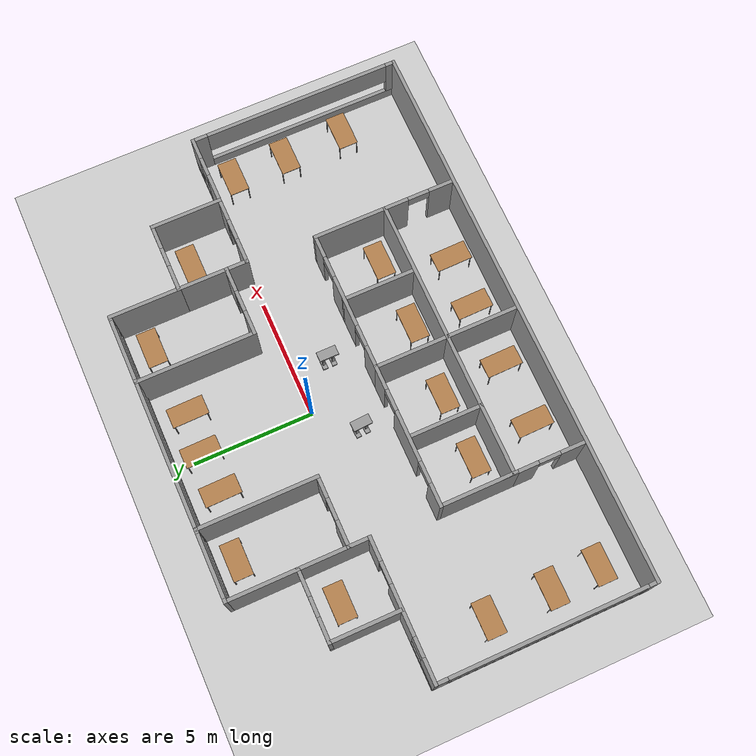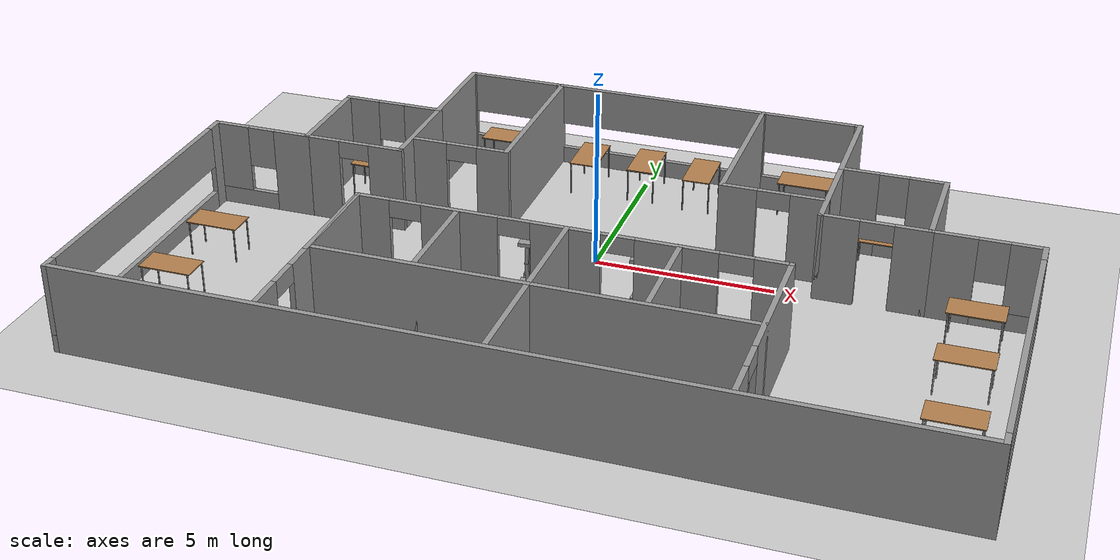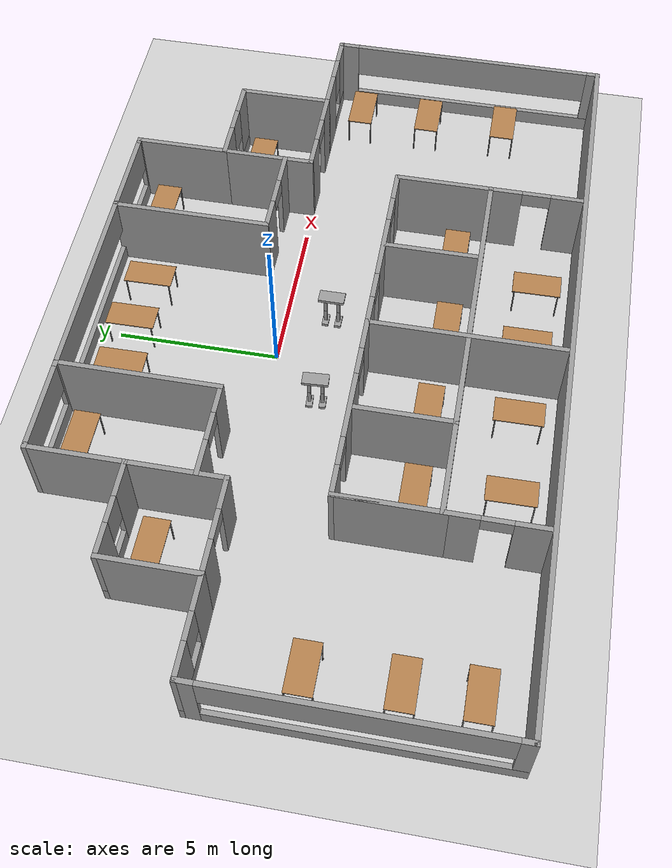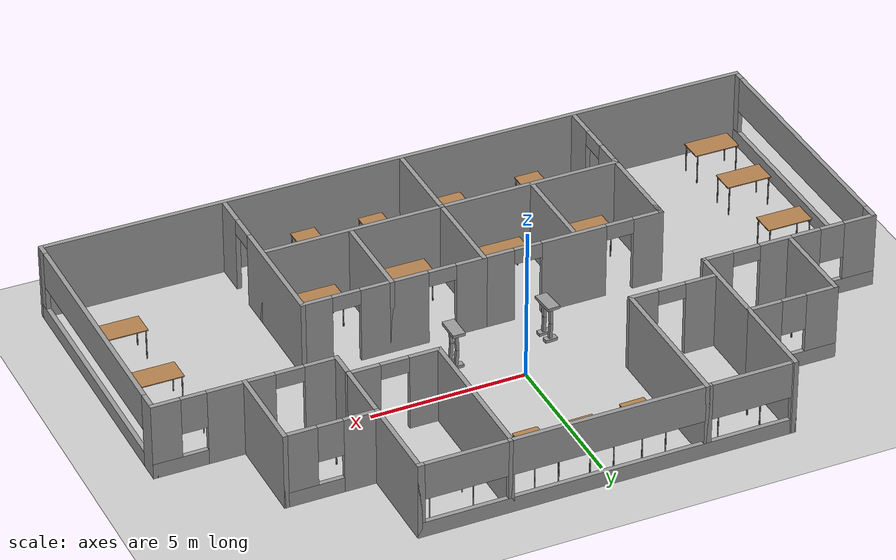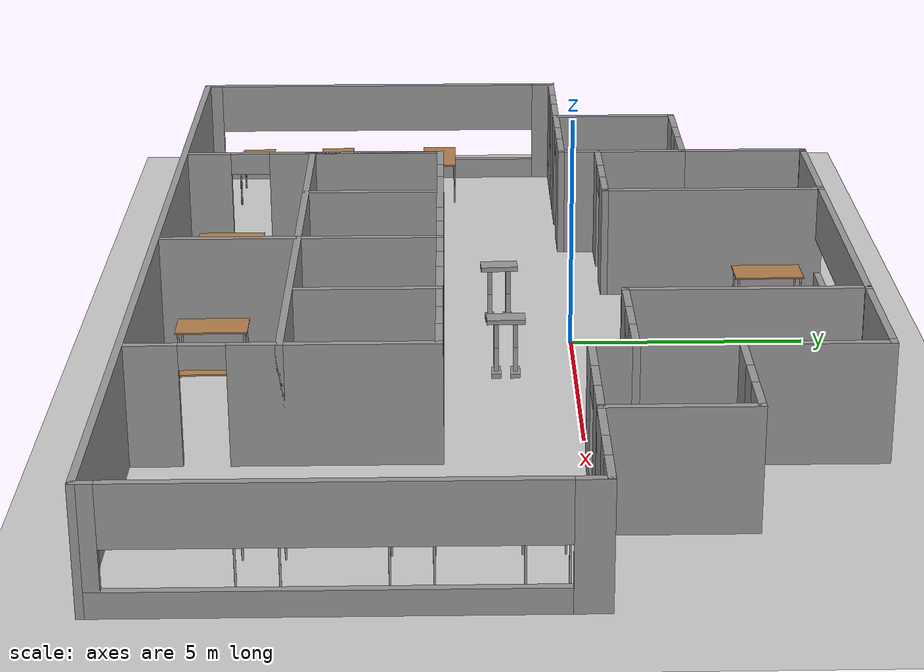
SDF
<sdf version="1.6">
 <world name="default">
  <plugin name="welcome_message" filename="libwelcome_message.so"/>
  <light name="sun" type="directional">
   <pose>0 0 10 0 -0 0</pose>
   <diffuse>0.8 0.8 0.8 1</diffuse>
   <specular>0.1 0.1 0.1 1</specular>
   <attenuation>
    <range>1000</range>
    <constant>0.9</constant>
    <linear>0.01</linear>
    <quadratic>0.001</quadratic>
   </attenuation>
   <direction>-0.5 0.5 -1</direction>
  </light>
  <model name="ground_plane">
   <static>1</static>
   <link name="link">
    <collision name="collision">
     <geometry><plane><normal>0 0 1</normal><size>100 100</size></plane></geometry>
     <surface><friction><ode><mu>100</mu><mu2>50</mu2></ode></friction></surface>
    </collision>
    <visual name="visual">
     <cast_shadows>0</cast_shadows>
     <geometry><plane><normal>0 0 1</normal><size>100 100</size></plane></geometry>
     <material>
      <script><uri>file://media/materials/scripts/gazebo.material</uri><name>Gazebo/Grey</name></script>
     </material>
    </visual>
   </link>
  </model>
  <gravity>0 0 -9.8</gravity>
  <magnetic_field>6e-06 2.3e-05 -4.2e-05</magnetic_field>
  <atmosphere type="adiabatic"/>
  <physics name="default_physics" default="0" type="ode">
   <max_step_size>0.001</max_step_size>
   <real_time_factor>1</real_time_factor>
   <real_time_update_rate>1000</real_time_update_rate>
  </physics>
  <scene><ambient>0.4 0.4 0.4 1</ambient><background>0.7 0.7 0.7 1</background><shadows>1</shadows></scene>
  <spherical_coordinates>
   <surface_model>EARTH_WGS84</surface_model>
   <latitude_deg>0</latitude_deg>
   <longitude_deg>0</longitude_deg>
   <elevation>0</elevation>
   <heading_deg>0</heading_deg>
  </spherical_coordinates>
  <model name="my_world">
   <pose>0.149259 -1.52681 0 0 -0 0</pose>
   <link name="Wall_11">
    <pose>-0 7.275 0 0 -0 0</pose>
    <visual name="Wall_11_Visual_0">
     <pose>-5.9021 0 1.25 0 -0 0</pose>
     <geometry><box><size>0.195806 0.15 2.5</size></box></geometry>
     <material>
      <script><uri>file://media/materials/scripts/gazebo.material</uri><name>Gazebo/Grey</name></script>
      <ambient>1 1 1 1</ambient>
     </material>
     <meta><layer>0</layer></meta>
    </visual>
    <collision name="Wall_11_Collision_0">
     <geometry><box><size>0.195806 0.15 2.5</size></box></geometry>
     <pose>-5.9021 0 1.25 0 -0 0</pose>
    </collision>
    <visual name="Wall_11_Visual_1">
     <pose>0.097903 0 0.25 0 -0 0</pose>
     <geometry><box><size>11.8042 0.15 0.5</size></box></geometry>
     <material>
      <script><uri>file://media/materials/scripts/gazebo.material</uri><name>Gazebo/Grey</name></script>
      <ambient>1 1 1 1</ambient>
     </material>
     <meta><layer>0</layer></meta>
    </visual>
    <collision name="Wall_11_Collision_1">
     <geometry><box><size>11.8042 0.15 0.5</size></box></geometry>
     <pose>0.097903 0 0.25 0 -0 0</pose>
    </collision>
    <visual name="Wall_11_Visual_2">
     <pose>-3.13049 0 1.5 0 -0 0</pose>
     <geometry><box><size>0.214424 0.15 2</size></box></geometry>
     <material>
      <script><uri>file://media/materials/scripts/gazebo.material</uri><name>Gazebo/Grey</name></script>
      <ambient>1 1 1 1</ambient>
     </material>
     <meta><layer>0</layer></meta>
    </visual>
    <collision name="Wall_11_Collision_2">
     <geometry><box><size>0.214424 0.15 2</size></box></geometry>
     <pose>-3.13049 0 1.5 0 -0 0</pose>
    </collision>
    <visual name="Wall_11_Visual_3">
     <pose>3.12221 0 1.5 0 -0 0</pose>
     <geometry><box><size>0.126973 0.15 2</size></box></geometry>
     <material>
      <script><uri>file://media/materials/scripts/gazebo.material</uri><name>Gazebo/Grey</name></script>
      <ambient>1 1 1 1</ambient>
     </material>
     <meta><layer>0</layer></meta>
    </visual>
    <collision name="Wall_11_Collision_3">
     <geometry><box><size>0.126973 0.15 2</size></box></geometry>
     <pose>3.12221 0 1.5 0 -0 0</pose>
    </collision>
    <visual name="Wall_11_Visual_4">
     <pose>5.88484 0 1.5 0 -0 0</pose>
     <geometry><box><size>0.230316 0.15 2</size></box></geometry>
     <material>
      <script><uri>file://media/materials/scripts/gazebo.material</uri><name>Gazebo/Grey</name></script>
      <ambient>1 1 1 1</ambient>
     </material>
     <meta><layer>0</layer></meta>
    </visual>
    <collision name="Wall_11_Collision_4">
     <geometry><box><size>0.230316 0.15 2</size></box></geometry>
     <pose>5.88484 0 1.5 0 -0 0</pose>
    </collision>
    <visual name="Wall_11_Visual_5">
     <pose>-4.52095 0 1.9 0 -0 0</pose>
     <geometry><box><size>2.5665 0.15 1.2</size></box></geometry>
     <material>
      <script><uri>file://media/materials/scripts/gazebo.material</uri><name>Gazebo/Grey</name></script>
      <ambient>1 1 1 1</ambient>
     </material>
     <meta><layer>0</layer></meta>
    </visual>
    <collision name="Wall_11_Collision_5">
     <geometry><box><size>2.5665 0.15 1.2</size></box></geometry>
     <pose>-4.52095 0 1.9 0 -0 0</pose>
    </collision>
    <visual name="Wall_11_Visual_6">
     <pose>0.017725 0 1.9 0 -0 0</pose>
     <geometry><box><size>6.082 0.15 1.2</size></box></geometry>
     <material>
      <script><uri>file://media/materials/scripts/gazebo.material</uri><name>Gazebo/Grey</name></script>
      <ambient>1 1 1 1</ambient>
     </material>
     <meta><layer>0</layer></meta>
    </visual>
    <collision name="Wall_11_Collision_6">
     <geometry><box><size>6.082 0.15 1.2</size></box></geometry>
     <pose>0.017725 0 1.9 0 -0 0</pose>
    </collision>
    <visual name="Wall_11_Visual_7">
     <pose>4.47769 0 1.9 0 -0 0</pose>
     <geometry><box><size>2.58399 0.15 1.2</size></box></geometry>
     <material>
      <script><uri>file://media/materials/scripts/gazebo.material</uri><name>Gazebo/Grey</name></script>
      <ambient>1 1 1 1</ambient>
     </material>
     <meta><layer>0</layer></meta>
    </visual>
    <collision name="Wall_11_Collision_7">
     <geometry><box><size>2.58399 0.15 1.2</size></box></geometry>
     <pose>4.47769 0 1.9 0 -0 0</pose>
    </collision>
   </link>
   <link name="Wall_12">
    <collision name="Wall_12_Collision">
     <geometry><box><size>3 0.15 2.5</size></box></geometry>
     <pose>0 0 1.25 0 -0 0</pose>
    </collision>
    <visual name="Wall_12_Visual">
     <pose>0 0 1.25 0 -0 0</pose>
     <geometry><box><size>3 0.15 2.5</size></box></geometry>
     <material>
      <script><uri>file://media/materials/scripts/gazebo.material</uri><name>Gazebo/Grey</name></script>
      <ambient>1 1 1 1</ambient>
     </material>
     <meta><layer>0</layer></meta>
    </visual>
    <pose>5.925 5.85 0 0 -0 -1.5708</pose>
   </link>
   <link name="Wall_15">
    <pose>7.35 4.425 0 0 -0 0</pose>
    <visual name="Wall_15_Visual_0">
     <pose>-0.934479 0 1.25 0 -0 0</pose>
     <geometry><box><size>1.13104 0.15 2.5</size></box></geometry>
     <material>
      <script><uri>file://media/materials/scripts/gazebo.material</uri><name>Gazebo/Grey</name></script>
      <ambient>1 1 1 1</ambient>
     </material>
     <meta><layer>0</layer></meta>
    </visual>
    <collision name="Wall_15_Collision_0">
     <geometry><box><size>1.13104 0.15 2.5</size></box></geometry>
     <pose>-0.934479 0 1.25 0 -0 0</pose>
    </collision>
    <visual name="Wall_15_Visual_1">
     <pose>0.565521 0 0.25 0 -0 0</pose>
     <geometry><box><size>1.86896 0.15 0.5</size></box></geometry>
     <material>
      <script><uri>file://media/materials/scripts/gazebo.material</uri><name>Gazebo/Grey</name></script>
      <ambient>1 1 1 1</ambient>
     </material>
     <meta><layer>0</layer></meta>
    </visual>
    <collision name="Wall_15_Collision_1">
     <geometry><box><size>1.86896 0.15 0.5</size></box></geometry>
     <pose>0.565521 0 0.25 0 -0 0</pose>
    </collision>
    <visual name="Wall_15_Visual_2">
     <pose>0.965521 0 1.5 0 -0 0</pose>
     <geometry><box><size>1.06896 0.15 2</size></box></geometry>
     <material>
      <script><uri>file://media/materials/scripts/gazebo.material</uri><name>Gazebo/Grey</name></script>
      <ambient>1 1 1 1</ambient>
     </material>
     <meta><layer>0</layer></meta>
    </visual>
    <collision name="Wall_15_Collision_2">
     <geometry><box><size>1.06896 0.15 2</size></box></geometry>
     <pose>0.965521 0 1.5 0 -0 0</pose>
    </collision>
    <visual name="Wall_15_Visual_3">
     <pose>0.031041 0 1.9 0 -0 0</pose>
     <geometry><box><size>0.8 0.15 1.2</size></box></geometry>
     <material>
      <script><uri>file://media/materials/scripts/gazebo.material</uri><name>Gazebo/Grey</name></script>
      <ambient>1 1 1 1</ambient>
     </material>
     <meta><layer>0</layer></meta>
    </visual>
    <collision name="Wall_15_Collision_3">
     <geometry><box><size>0.8 0.15 1.2</size></box></geometry>
     <pose>0.031041 0 1.9 0 -0 0</pose>
    </collision>
   </link>
   <link name="Wall_16">
    <collision name="Wall_16_Collision">
     <geometry><box><size>3 0.15 2.5</size></box></geometry>
     <pose>0 0 1.25 0 -0 0</pose>
    </collision>
    <visual name="Wall_16_Visual">
     <pose>0 0 1.25 0 -0 0</pose>
     <geometry><box><size>3 0.15 2.5</size></box></geometry>
     <material>
      <script><uri>file://media/materials/scripts/gazebo.material</uri><name>Gazebo/Grey</name></script>
      <ambient>1 1 1 1</ambient>
     </material>
     <meta><layer>0</layer></meta>
    </visual>
    <pose>8.775 3 0 0 -0 -1.5708</pose>
   </link>
   <link name="Wall_17">
    <pose>10.2 1.575 0 0 -0 0</pose>
    <visual name="Wall_17_Visual_0">
     <pose>-0.864079 0 1.25 0 -0 0</pose>
     <geometry><box><size>1.27184 0.15 2.5</size></box></geometry>
     <material>
      <script><uri>file://media/materials/scripts/gazebo.material</uri><name>Gazebo/Grey</name></script>
      <ambient>1 1 1 1</ambient>
     </material>
     <meta><layer>0</layer></meta>
    </visual>
    <collision name="Wall_17_Collision_0">
     <geometry><box><size>1.27184 0.15 2.5</size></box></geometry>
     <pose>-0.864079 0 1.25 0 -0 0</pose>
    </collision>
    <visual name="Wall_17_Visual_1">
     <pose>0.635921 0 0.25 0 -0 0</pose>
     <geometry><box><size>1.72816 0.15 0.5</size></box></geometry>
     <material>
      <script><uri>file://media/materials/scripts/gazebo.material</uri><name>Gazebo/Grey</name></script>
      <ambient>1 1 1 1</ambient>
     </material>
     <meta><layer>0</layer></meta>
    </visual>
    <collision name="Wall_17_Collision_1">
     <geometry><box><size>1.72816 0.15 0.5</size></box></geometry>
     <pose>0.635921 0 0.25 0 -0 0</pose>
    </collision>
    <visual name="Wall_17_Visual_2">
     <pose>1.03592 0 1.5 0 -0 0</pose>
     <geometry><box><size>0.928158 0.15 2</size></box></geometry>
     <material>
      <script><uri>file://media/materials/scripts/gazebo.material</uri><name>Gazebo/Grey</name></script>
      <ambient>1 1 1 1</ambient>
     </material>
     <meta><layer>0</layer></meta>
    </visual>
    <collision name="Wall_17_Collision_2">
     <geometry><box><size>0.928158 0.15 2</size></box></geometry>
     <pose>1.03592 0 1.5 0 -0 0</pose>
    </collision>
    <visual name="Wall_17_Visual_3">
     <pose>0.171842 0 1.9 0 -0 0</pose>
     <geometry><box><size>0.8 0.15 1.2</size></box></geometry>
     <material>
      <script><uri>file://media/materials/scripts/gazebo.material</uri><name>Gazebo/Grey</name></script>
      <ambient>1 1 1 1</ambient>
     </material>
     <meta><layer>0</layer></meta>
    </visual>
    <collision name="Wall_17_Collision_3">
     <geometry><box><size>0.8 0.15 1.2</size></box></geometry>
     <pose>0.171842 0 1.9 0 -0 0</pose>
    </collision>
   </link>
   <link name="Wall_30">
    <collision name="Wall_30_Collision">
     <geometry><box><size>3 0.15 2.5</size></box></geometry>
     <pose>0 0 1.25 0 -0 0</pose>
    </collision>
    <visual name="Wall_30_Visual">
     <pose>0 0 1.25 0 -0 0</pose>
     <geometry><box><size>3 0.15 2.5</size></box></geometry>
     <material>
      <script><uri>file://media/materials/scripts/gazebo.material</uri><name>Gazebo/Grey</name></script>
      <ambient>1 1 1 1</ambient>
     </material>
     <meta><layer>0</layer></meta>
    </visual>
    <pose>5.925 3 0 0 -0 -1.5708</pose>
   </link>
   <link name="Wall_31">
    <pose>7.35 1.575 0 0 -0 0</pose>
    <visual name="Wall_31_Visual_0">
     <pose>-0.950393 0 1.25 0 -0 0</pose>
     <geometry><box><size>1.09921 0.15 2.5</size></box></geometry>
     <material>
      <script><uri>file://media/materials/scripts/gazebo.material</uri><name>Gazebo/Grey</name></script>
      <ambient>1 1 1 1</ambient>
     </material>
     <meta><layer>0</layer></meta>
    </visual>
    <collision name="Wall_31_Collision_0">
     <geometry><box><size>1.09921 0.15 2.5</size></box></geometry>
     <pose>-0.950393 0 1.25 0 -0 0</pose>
    </collision>
    <visual name="Wall_31_Visual_1">
     <pose>0.999607 0 1.25 0 -0 0</pose>
     <geometry><box><size>1.00079 0.15 2.5</size></box></geometry>
     <material>
      <script><uri>file://media/materials/scripts/gazebo.material</uri><name>Gazebo/Grey</name></script>
      <ambient>1 1 1 1</ambient>
     </material>
     <meta><layer>0</layer></meta>
    </visual>
    <collision name="Wall_31_Collision_1">
     <geometry><box><size>1.00079 0.15 2.5</size></box></geometry>
     <pose>0.999607 0 1.25 0 -0 0</pose>
    </collision>
    <visual name="Wall_31_Visual_2">
     <pose>0.049213 0 2.25 0 -0 0</pose>
     <geometry><box><size>0.9 0.15 0.5</size></box></geometry>
     <material>
      <script><uri>file://media/materials/scripts/gazebo.material</uri><name>Gazebo/Grey</name></script>
      <ambient>1 1 1 1</ambient>
     </material>
     <meta><layer>0</layer></meta>
    </visual>
    <collision name="Wall_31_Collision_2">
     <geometry><box><size>0.9 0.15 0.5</size></box></geometry>
     <pose>0.049213 0 2.25 0 -0 0</pose>
    </collision>
   </link>
   <link name="Wall_34">
    <collision name="Wall_34_Collision">
     <geometry><box><size>5 0.15 2.5</size></box></geometry>
     <pose>0 0 1.25 0 -0 0</pose>
    </collision>
    <visual name="Wall_34_Visual">
     <pose>0 0 1.25 0 -0 0</pose>
     <geometry><box><size>5 0.15 2.5</size></box></geometry>
     <material>
      <script><uri>file://media/materials/scripts/gazebo.material</uri><name>Gazebo/Grey</name></script>
      <ambient>1 1 1 1</ambient>
     </material>
     <meta><layer>0</layer></meta>
    </visual>
    <pose>3.075 4.85 0 0 -0 -1.5708</pose>
   </link>
   <link name="Wall_35">
    <pose>4.5 2.425 0 0 -0 0</pose>
    <visual name="Wall_35_Visual_0">
     <pose>-0.977068 0 1.25 0 -0 0</pose>
     <geometry><box><size>1.04586 0.15 2.5</size></box></geometry>
     <material>
      <script><uri>file://media/materials/scripts/gazebo.material</uri><name>Gazebo/Grey</name></script>
      <ambient>1 1 1 1</ambient>
     </material>
     <meta><layer>0</layer></meta>
    </visual>
    <collision name="Wall_35_Collision_0">
     <geometry><box><size>1.04586 0.15 2.5</size></box></geometry>
     <pose>-0.977068 0 1.25 0 -0 0</pose>
    </collision>
    <visual name="Wall_35_Visual_1">
     <pose>0.972932 0 1.25 0 -0 0</pose>
     <geometry><box><size>1.05414 0.15 2.5</size></box></geometry>
     <material>
      <script><uri>file://media/materials/scripts/gazebo.material</uri><name>Gazebo/Grey</name></script>
      <ambient>1 1 1 1</ambient>
     </material>
     <meta><layer>0</layer></meta>
    </visual>
    <collision name="Wall_35_Collision_1">
     <geometry><box><size>1.05414 0.15 2.5</size></box></geometry>
     <pose>0.972932 0 1.25 0 -0 0</pose>
    </collision>
    <visual name="Wall_35_Visual_2">
     <pose>-0.004137 0 2.25 0 -0 0</pose>
     <geometry><box><size>0.9 0.15 0.5</size></box></geometry>
     <material>
      <script><uri>file://media/materials/scripts/gazebo.material</uri><name>Gazebo/Grey</name></script>
      <ambient>1 1 1 1</ambient>
     </material>
     <meta><layer>0</layer></meta>
    </visual>
    <collision name="Wall_35_Collision_2">
     <geometry><box><size>0.9 0.15 0.5</size></box></geometry>
     <pose>-0.004137 0 2.25 0 -0 0</pose>
    </collision>
   </link>
   <link name="Wall_39">
    <pose>2.85 -1.275 0 0 -0 3.14159</pose>
    <visual name="Wall_39_Visual_0">
     <pose>-2.4945 0 1.25 0 -0 0</pose>
     <geometry><box><size>1.01101 0.15 2.5</size></box></geometry>
     <material>
      <script><uri>file://media/materials/scripts/gazebo.material</uri><name>Gazebo/Grey</name></script>
      <ambient>1 1 1 1</ambient>
     </material>
     <meta><layer>0</layer></meta>
    </visual>
    <collision name="Wall_39_Collision_0">
     <geometry><box><size>1.01101 0.15 2.5</size></box></geometry>
     <pose>-2.4945 0 1.25 0 -0 0</pose>
    </collision>
    <visual name="Wall_39_Visual_1">
     <pose>0.008881 0 1.25 0 -0 0</pose>
     <geometry><box><size>2.19574 0.15 2.5</size></box></geometry>
     <material>
      <script><uri>file://media/materials/scripts/gazebo.material</uri><name>Gazebo/Grey</name></script>
      <ambient>1 1 1 1</ambient>
     </material>
     <meta><layer>0</layer></meta>
    </visual>
    <collision name="Wall_39_Collision_1">
     <geometry><box><size>2.19574 0.15 2.5</size></box></geometry>
     <pose>0.008881 0 1.25 0 -0 0</pose>
    </collision>
    <visual name="Wall_39_Visual_2">
     <pose>2.50338 0 1.25 0 -0 0</pose>
     <geometry><box><size>0.993249 0.15 2.5</size></box></geometry>
     <material>
      <script><uri>file://media/materials/scripts/gazebo.material</uri><name>Gazebo/Grey</name></script>
      <ambient>1 1 1 1</ambient>
     </material>
     <meta><layer>0</layer></meta>
    </visual>
    <collision name="Wall_39_Collision_2">
     <geometry><box><size>0.993249 0.15 2.5</size></box></geometry>
     <pose>2.50338 0 1.25 0 -0 0</pose>
    </collision>
    <visual name="Wall_39_Visual_3">
     <pose>-1.53899 0 2.25 0 -0 0</pose>
     <geometry><box><size>0.9 0.15 0.5</size></box></geometry>
     <material>
      <script><uri>file://media/materials/scripts/gazebo.material</uri><name>Gazebo/Grey</name></script>
      <ambient>1 1 1 1</ambient>
     </material>
     <meta><layer>0</layer></meta>
    </visual>
    <collision name="Wall_39_Collision_3">
     <geometry><box><size>0.9 0.15 0.5</size></box></geometry>
     <pose>-1.53899 0 2.25 0 -0 0</pose>
    </collision>
    <visual name="Wall_39_Visual_4">
     <pose>1.55675 0 2.25 0 -0 0</pose>
     <geometry><box><size>0.9 0.15 0.5</size></box></geometry>
     <material>
      <script><uri>file://media/materials/scripts/gazebo.material</uri><name>Gazebo/Grey</name></script>
      <ambient>1 1 1 1</ambient>
     </material>
     <meta><layer>0</layer></meta>
    </visual>
    <collision name="Wall_39_Collision_4">
     <geometry><box><size>0.9 0.15 0.5</size></box></geometry>
     <pose>1.55675 0 2.25 0 -0 0</pose>
    </collision>
   </link>
   <link name="Wall_40">
    <collision name="Wall_40_Collision">
     <geometry><box><size>6 0.15 2.5</size></box></geometry>
     <pose>0 0 1.25 0 -0 0</pose>
    </collision>
    <visual name="Wall_40_Visual">
     <pose>0 0 1.25 0 -0 0</pose>
     <geometry><box><size>6 0.15 2.5</size></box></geometry>
     <material>
      <script><uri>file://media/materials/scripts/gazebo.material</uri><name>Gazebo/Grey</name></script>
      <ambient>1 1 1 1</ambient>
     </material>
     <meta><layer>0</layer></meta>
    </visual>
    <pose>-0.075 -4.2 0 0 -0 -1.5708</pose>
   </link>
   <link name="Wall_45">
    <collision name="Wall_45_Collision">
     <geometry><box><size>6 0.15 2.5</size></box></geometry>
     <pose>0 0 1.25 0 -0 0</pose>
    </collision>
    <visual name="Wall_45_Visual">
     <pose>0 0 1.25 0 -0 0</pose>
     <geometry><box><size>6 0.15 2.5</size></box></geometry>
     <material>
      <script><uri>file://media/materials/scripts/gazebo.material</uri><name>Gazebo/Grey</name></script>
      <ambient>1 1 1 1</ambient>
     </material>
     <meta><layer>0</layer></meta>
    </visual>
    <pose>2.85 -4.275 0 0 -0 0</pose>
   </link>
   <link name="Wall_48">
    <collision name="Wall_48_Collision">
     <geometry><box><size>3 0.15 2.5</size></box></geometry>
     <pose>0 0 1.25 0 -0 0</pose>
    </collision>
    <visual name="Wall_48_Visual">
     <pose>0 0 1.25 0 -0 0</pose>
     <geometry><box><size>3 0.15 2.5</size></box></geometry>
     <material>
      <script><uri>file://media/materials/scripts/gazebo.material</uri><name>Gazebo/Grey</name></script>
      <ambient>1 1 1 1</ambient>
     </material>
     <meta><layer>0</layer></meta>
    </visual>
    <pose>2.925 -2.7 0 0 -0 -1.5708</pose>
   </link>
   <link name="Wall_54">
    <collision name="Wall_54_Collision">
     <geometry><box><size>3 0.15 2.5</size></box></geometry>
     <pose>0 0 1.25 0 -0 0</pose>
    </collision>
    <visual name="Wall_54_Visual">
     <pose>0 0 1.25 0 -0 0</pose>
     <geometry><box><size>3 0.15 2.5</size></box></geometry>
     <material>
      <script><uri>file://media/materials/scripts/gazebo.material</uri><name>Gazebo/Grey</name></script>
      <ambient>1 1 1 1</ambient>
     </material>
     <meta><layer>0</layer></meta>
    </visual>
    <pose>-5.925 5.85 0 0 -0 -1.5708</pose>
   </link>
   <link name="Wall_55">
    <pose>-7.35 4.425 0 0 -0 3.14159</pose>
    <visual name="Wall_55_Visual_0">
     <pose>-0.925969 0 1.25 0 -0 0</pose>
     <geometry><box><size>1.14806 0.15 2.5</size></box></geometry>
     <material>
      <script><uri>file://media/materials/scripts/gazebo.material</uri><name>Gazebo/Grey</name></script>
      <ambient>1 1 1 1</ambient>
     </material>
     <meta><layer>0</layer></meta>
    </visual>
    <collision name="Wall_55_Collision_0">
     <geometry><box><size>1.14806 0.15 2.5</size></box></geometry>
     <pose>-0.925969 0 1.25 0 -0 0</pose>
    </collision>
    <visual name="Wall_55_Visual_1">
     <pose>0.574031 0 0.25 0 -0 0</pose>
     <geometry><box><size>1.85194 0.15 0.5</size></box></geometry>
     <material>
      <script><uri>file://media/materials/scripts/gazebo.material</uri><name>Gazebo/Grey</name></script>
      <ambient>1 1 1 1</ambient>
     </material>
     <meta><layer>0</layer></meta>
    </visual>
    <collision name="Wall_55_Collision_1">
     <geometry><box><size>1.85194 0.15 0.5</size></box></geometry>
     <pose>0.574031 0 0.25 0 -0 0</pose>
    </collision>
    <visual name="Wall_55_Visual_2">
     <pose>0.974031 0 1.5 0 -0 0</pose>
     <geometry><box><size>1.05194 0.15 2</size></box></geometry>
     <material>
      <script><uri>file://media/materials/scripts/gazebo.material</uri><name>Gazebo/Grey</name></script>
      <ambient>1 1 1 1</ambient>
     </material>
     <meta><layer>0</layer></meta>
    </visual>
    <collision name="Wall_55_Collision_2">
     <geometry><box><size>1.05194 0.15 2</size></box></geometry>
     <pose>0.974031 0 1.5 0 -0 0</pose>
    </collision>
    <visual name="Wall_55_Visual_3">
     <pose>0.048061 0 1.9 0 -0 0</pose>
     <geometry><box><size>0.8 0.15 1.2</size></box></geometry>
     <material>
      <script><uri>file://media/materials/scripts/gazebo.material</uri><name>Gazebo/Grey</name></script>
      <ambient>1 1 1 1</ambient>
     </material>
     <meta><layer>0</layer></meta>
    </visual>
    <collision name="Wall_55_Collision_3">
     <geometry><box><size>0.8 0.15 1.2</size></box></geometry>
     <pose>0.048061 0 1.9 0 -0 0</pose>
    </collision>
   </link>
   <link name="Wall_56">
    <collision name="Wall_56_Collision">
     <geometry><box><size>3 0.15 2.5</size></box></geometry>
     <pose>0 0 1.25 0 -0 0</pose>
    </collision>
    <visual name="Wall_56_Visual">
     <pose>0 0 1.25 0 -0 0</pose>
     <geometry><box><size>3 0.15 2.5</size></box></geometry>
     <material>
      <script><uri>file://media/materials/scripts/gazebo.material</uri><name>Gazebo/Grey</name></script>
      <ambient>1 1 1 1</ambient>
     </material>
     <meta><layer>0</layer></meta>
    </visual>
    <pose>-8.775 3 0 0 -0 -1.5708</pose>
   </link>
   <link name="Wall_57">
    <pose>-10.2 1.575 0 0 -0 3.14159</pose>
    <visual name="Wall_57_Visual_0">
     <pose>-0.94302 0 1.25 0 -0 0</pose>
     <geometry><box><size>1.11396 0.15 2.5</size></box></geometry>
     <material>
      <script><uri>file://media/materials/scripts/gazebo.material</uri><name>Gazebo/Grey</name></script>
      <ambient>1 1 1 1</ambient>
     </material>
     <meta><layer>0</layer></meta>
    </visual>
    <collision name="Wall_57_Collision_0">
     <geometry><box><size>1.11396 0.15 2.5</size></box></geometry>
     <pose>-0.94302 0 1.25 0 -0 0</pose>
    </collision>
    <visual name="Wall_57_Visual_1">
     <pose>0.55698 0 0.25 0 -0 0</pose>
     <geometry><box><size>1.88604 0.15 0.5</size></box></geometry>
     <material>
      <script><uri>file://media/materials/scripts/gazebo.material</uri><name>Gazebo/Grey</name></script>
      <ambient>1 1 1 1</ambient>
     </material>
     <meta><layer>0</layer></meta>
    </visual>
    <collision name="Wall_57_Collision_1">
     <geometry><box><size>1.88604 0.15 0.5</size></box></geometry>
     <pose>0.55698 0 0.25 0 -0 0</pose>
    </collision>
    <visual name="Wall_57_Visual_2">
     <pose>0.95698 0 1.5 0 -0 0</pose>
     <geometry><box><size>1.08604 0.15 2</size></box></geometry>
     <material>
      <script><uri>file://media/materials/scripts/gazebo.material</uri><name>Gazebo/Grey</name></script>
      <ambient>1 1 1 1</ambient>
     </material>
     <meta><layer>0</layer></meta>
    </visual>
    <collision name="Wall_57_Collision_2">
     <geometry><box><size>1.08604 0.15 2</size></box></geometry>
     <pose>0.95698 0 1.5 0 -0 0</pose>
    </collision>
    <visual name="Wall_57_Visual_3">
     <pose>0.013961 0 1.9 0 -0 0</pose>
     <geometry><box><size>0.8 0.15 1.2</size></box></geometry>
     <material>
      <script><uri>file://media/materials/scripts/gazebo.material</uri><name>Gazebo/Grey</name></script>
      <ambient>1 1 1 1</ambient>
     </material>
     <meta><layer>0</layer></meta>
    </visual>
    <collision name="Wall_57_Collision_3">
     <geometry><box><size>0.8 0.15 1.2</size></box></geometry>
     <pose>0.013961 0 1.9 0 -0 0</pose>
    </collision>
   </link>
   <link name="Wall_59">
    <pose>-11.625 -2.85 0 0 -0 -1.5708</pose>
    <visual name="Wall_59_Visual_0">
     <pose>-4.21718 0 1.25 0 -0 0</pose>
     <geometry><box><size>0.565642 0.15 2.5</size></box></geometry>
     <material>
      <script><uri>file://media/materials/scripts/gazebo.material</uri><name>Gazebo/Grey</name></script>
      <ambient>1 1 1 1</ambient>
     </material>
     <meta><layer>0</layer></meta>
    </visual>
    <collision name="Wall_59_Collision_0">
     <geometry><box><size>0.565642 0.15 2.5</size></box></geometry>
     <pose>-4.21718 0 1.25 0 -0 0</pose>
    </collision>
    <visual name="Wall_59_Visual_1">
     <pose>0.282821 0 0.25 0 -0 0</pose>
     <geometry><box><size>8.43436 0.15 0.5</size></box></geometry>
     <material>
      <script><uri>file://media/materials/scripts/gazebo.material</uri><name>Gazebo/Grey</name></script>
      <ambient>1 1 1 1</ambient>
     </material>
     <meta><layer>0</layer></meta>
    </visual>
    <collision name="Wall_59_Collision_1">
     <geometry><box><size>8.43436 0.15 0.5</size></box></geometry>
     <pose>0.282821 0 0.25 0 -0 0</pose>
    </collision>
    <visual name="Wall_59_Visual_2">
     <pose>4.27963 0 1.5 0 -0 0</pose>
     <geometry><box><size>0.440739 0.15 2</size></box></geometry>
     <material>
      <script><uri>file://media/materials/scripts/gazebo.material</uri><name>Gazebo/Grey</name></script>
      <ambient>1 1 1 1</ambient>
     </material>
     <meta><layer>0</layer></meta>
    </visual>
    <collision name="Wall_59_Collision_2">
     <geometry><box><size>0.440739 0.15 2</size></box></geometry>
     <pose>4.27963 0 1.5 0 -0 0</pose>
    </collision>
    <visual name="Wall_59_Visual_3">
     <pose>0.062451 0 1.9 0 -0 0</pose>
     <geometry><box><size>7.99362 0.15 1.2</size></box></geometry>
     <material>
      <script><uri>file://media/materials/scripts/gazebo.material</uri><name>Gazebo/Grey</name></script>
      <ambient>1 1 1 1</ambient>
     </material>
     <meta><layer>0</layer></meta>
    </visual>
    <collision name="Wall_59_Collision_3">
     <geometry><box><size>7.99362 0.15 1.2</size></box></geometry>
     <pose>0.062451 0 1.9 0 -0 0</pose>
    </collision>
   </link>
   <link name="Wall_61">
    <pose>11.625 -2.85 0 0 -0 -1.5708</pose>
    <visual name="Wall_61_Visual_0">
     <pose>-4.15935 0 1.25 0 -0 0</pose>
     <geometry><box><size>0.681295 0.15 2.5</size></box></geometry>
     <material>
      <script><uri>file://media/materials/scripts/gazebo.material</uri><name>Gazebo/Grey</name></script>
      <ambient>1 1 1 1</ambient>
     </material>
     <meta><layer>0</layer></meta>
    </visual>
    <collision name="Wall_61_Collision_0">
     <geometry><box><size>0.681295 0.15 2.5</size></box></geometry>
     <pose>-4.15935 0 1.25 0 -0 0</pose>
    </collision>
    <visual name="Wall_61_Visual_1">
     <pose>0.340648 0 0.25 0 -0 0</pose>
     <geometry><box><size>8.3187 0.15 0.5</size></box></geometry>
     <material>
      <script><uri>file://media/materials/scripts/gazebo.material</uri><name>Gazebo/Grey</name></script>
      <ambient>1 1 1 1</ambient>
     </material>
     <meta><layer>0</layer></meta>
    </visual>
    <collision name="Wall_61_Collision_1">
     <geometry><box><size>8.3187 0.15 0.5</size></box></geometry>
     <pose>0.340648 0 0.25 0 -0 0</pose>
    </collision>
    <visual name="Wall_61_Visual_2">
     <pose>4.27963 0 1.5 0 -0 0</pose>
     <geometry><box><size>0.440739 0.15 2</size></box></geometry>
     <material>
      <script><uri>file://media/materials/scripts/gazebo.material</uri><name>Gazebo/Grey</name></script>
      <ambient>1 1 1 1</ambient>
     </material>
     <meta><layer>0</layer></meta>
    </visual>
    <collision name="Wall_61_Collision_2">
     <geometry><box><size>0.440739 0.15 2</size></box></geometry>
     <pose>4.27963 0 1.5 0 -0 0</pose>
    </collision>
    <visual name="Wall_61_Visual_3">
     <pose>0.120278 0 1.9 0 -0 0</pose>
     <geometry><box><size>7.87797 0.15 1.2</size></box></geometry>
     <material>
      <script><uri>file://media/materials/scripts/gazebo.material</uri><name>Gazebo/Grey</name></script>
      <ambient>1 1 1 1</ambient>
     </material>
     <meta><layer>0</layer></meta>
    </visual>
    <collision name="Wall_61_Collision_3">
     <geometry><box><size>7.87797 0.15 1.2</size></box></geometry>
     <pose>0.120278 0 1.9 0 -0 0</pose>
    </collision>
   </link>
   <link name="Wall_62">
    <collision name="Wall_62_Collision">
     <geometry><box><size>23.4 0.15 2.5</size></box></geometry>
     <pose>0 0 1.25 0 -0 0</pose>
    </collision>
    <visual name="Wall_62_Visual">
     <pose>0 0 1.25 0 -0 0</pose>
     <geometry><box><size>23.4 0.15 2.5</size></box></geometry>
     <material>
      <script><uri>file://media/materials/scripts/gazebo.material</uri><name>Gazebo/Grey</name></script>
      <ambient>1 1 1 1</ambient>
     </material>
     <meta><layer>0</layer></meta>
    </visual>
    <pose>-0 -7.275 0 0 -0 3.14159</pose>
   </link>
   <link name="Wall_64">
    <pose>5.775 -4.2 0 0 -0 -1.5708</pose>
    <visual name="Wall_64_Visual_0">
     <pose>-0.963173 0 1.25 0 -0 0</pose>
     <geometry><box><size>4.07365 0.15 2.5</size></box></geometry>
     <material>
      <script><uri>file://media/materials/scripts/gazebo.material</uri><name>Gazebo/Grey</name></script>
      <ambient>1 1 1 1</ambient>
     </material>
     <meta><layer>0</layer></meta>
    </visual>
    <collision name="Wall_64_Collision_0">
     <geometry><box><size>4.07365 0.15 2.5</size></box></geometry>
     <pose>-0.963173 0 1.25 0 -0 0</pose>
    </collision>
    <visual name="Wall_64_Visual_1">
     <pose>2.48683 0 1.25 0 -0 0</pose>
     <geometry><box><size>1.02635 0.15 2.5</size></box></geometry>
     <material>
      <script><uri>file://media/materials/scripts/gazebo.material</uri><name>Gazebo/Grey</name></script>
      <ambient>1 1 1 1</ambient>
     </material>
     <meta><layer>0</layer></meta>
    </visual>
    <collision name="Wall_64_Collision_1">
     <geometry><box><size>1.02635 0.15 2.5</size></box></geometry>
     <pose>2.48683 0 1.25 0 -0 0</pose>
    </collision>
    <visual name="Wall_64_Visual_2">
     <pose>1.52365 0 2.25 0 -0 0</pose>
     <geometry><box><size>0.9 0.15 0.5</size></box></geometry>
     <material>
      <script><uri>file://media/materials/scripts/gazebo.material</uri><name>Gazebo/Grey</name></script>
      <ambient>1 1 1 1</ambient>
     </material>
     <meta><layer>0</layer></meta>
    </visual>
    <collision name="Wall_64_Collision_2">
     <geometry><box><size>0.9 0.15 0.5</size></box></geometry>
     <pose>1.52365 0 2.25 0 -0 0</pose>
    </collision>
   </link>
   <link name="Wall_66">
    <pose>-3 -1.275 0 0 -0 3.14159</pose>
    <visual name="Wall_66_Visual_0">
     <pose>-2.47242 0 1.25 0 -0 0</pose>
     <geometry><box><size>1.05516 0.15 2.5</size></box></geometry>
     <material>
      <script><uri>file://media/materials/scripts/gazebo.material</uri><name>Gazebo/Grey</name></script>
      <ambient>1 1 1 1</ambient>
     </material>
     <meta><layer>0</layer></meta>
    </visual>
    <collision name="Wall_66_Collision_0">
     <geometry><box><size>1.05516 0.15 2.5</size></box></geometry>
     <pose>-2.47242 0 1.25 0 -0 0</pose>
    </collision>
    <visual name="Wall_66_Visual_1">
     <pose>0.026797 0 1.25 0 -0 0</pose>
     <geometry><box><size>2.14327 0.15 2.5</size></box></geometry>
     <material>
      <script><uri>file://media/materials/scripts/gazebo.material</uri><name>Gazebo/Grey</name></script>
      <ambient>1 1 1 1</ambient>
     </material>
     <meta><layer>0</layer></meta>
    </visual>
    <collision name="Wall_66_Collision_1">
     <geometry><box><size>2.14327 0.15 2.5</size></box></geometry>
     <pose>0.026797 0 1.25 0 -0 0</pose>
    </collision>
    <visual name="Wall_66_Visual_2">
     <pose>2.49922 0 1.25 0 -0 0</pose>
     <geometry><box><size>1.00157 0.15 2.5</size></box></geometry>
     <material>
      <script><uri>file://media/materials/scripts/gazebo.material</uri><name>Gazebo/Grey</name></script>
      <ambient>1 1 1 1</ambient>
     </material>
     <meta><layer>0</layer></meta>
    </visual>
    <collision name="Wall_66_Collision_2">
     <geometry><box><size>1.00157 0.15 2.5</size></box></geometry>
     <pose>2.49922 0 1.25 0 -0 0</pose>
    </collision>
    <visual name="Wall_66_Visual_3">
     <pose>-1.49484 0 2.25 0 -0 0</pose>
     <geometry><box><size>0.9 0.15 0.5</size></box></geometry>
     <material>
      <script><uri>file://media/materials/scripts/gazebo.material</uri><name>Gazebo/Grey</name></script>
      <ambient>1 1 1 1</ambient>
     </material>
     <meta><layer>0</layer></meta>
    </visual>
    <collision name="Wall_66_Collision_3">
     <geometry><box><size>0.9 0.15 0.5</size></box></geometry>
     <pose>-1.49484 0 2.25 0 -0 0</pose>
    </collision>
    <visual name="Wall_66_Visual_4">
     <pose>1.54843 0 2.25 0 -0 0</pose>
     <geometry><box><size>0.9 0.15 0.5</size></box></geometry>
     <material>
      <script><uri>file://media/materials/scripts/gazebo.material</uri><name>Gazebo/Grey</name></script>
      <ambient>1 1 1 1</ambient>
     </material>
     <meta><layer>0</layer></meta>
    </visual>
    <collision name="Wall_66_Collision_4">
     <geometry><box><size>0.9 0.15 0.5</size></box></geometry>
     <pose>1.54843 0 2.25 0 -0 0</pose>
    </collision>
   </link>
   <link name="Wall_67">
    <pose>-5.925 -4.2 0 0 -0 -1.5708</pose>
    <visual name="Wall_67_Visual_0">
     <pose>-0.954428 0 1.25 0 -0 0</pose>
     <geometry><box><size>4.09114 0.15 2.5</size></box></geometry>
     <material>
      <script><uri>file://media/materials/scripts/gazebo.material</uri><name>Gazebo/Grey</name></script>
      <ambient>1 1 1 1</ambient>
     </material>
     <meta><layer>0</layer></meta>
    </visual>
    <collision name="Wall_67_Collision_0">
     <geometry><box><size>4.09114 0.15 2.5</size></box></geometry>
     <pose>-0.954428 0 1.25 0 -0 0</pose>
    </collision>
    <visual name="Wall_67_Visual_1">
     <pose>2.49557 0 1.25 0 -0 0</pose>
     <geometry><box><size>1.00886 0.15 2.5</size></box></geometry>
     <material>
      <script><uri>file://media/materials/scripts/gazebo.material</uri><name>Gazebo/Grey</name></script>
      <ambient>1 1 1 1</ambient>
     </material>
     <meta><layer>0</layer></meta>
    </visual>
    <collision name="Wall_67_Collision_1">
     <geometry><box><size>1.00886 0.15 2.5</size></box></geometry>
     <pose>2.49557 0 1.25 0 -0 0</pose>
    </collision>
    <visual name="Wall_67_Visual_2">
     <pose>1.54114 0 2.25 0 -0 0</pose>
     <geometry><box><size>0.9 0.15 0.5</size></box></geometry>
     <material>
      <script><uri>file://media/materials/scripts/gazebo.material</uri><name>Gazebo/Grey</name></script>
      <ambient>1 1 1 1</ambient>
     </material>
     <meta><layer>0</layer></meta>
    </visual>
    <collision name="Wall_67_Collision_2">
     <geometry><box><size>0.9 0.15 0.5</size></box></geometry>
     <pose>1.54114 0 2.25 0 -0 0</pose>
    </collision>
   </link>
   <link name="Wall_69">
    <collision name="Wall_69_Collision">
     <geometry><box><size>3.25 0.15 2.5</size></box></geometry>
     <pose>0 0 1.25 0 -0 0</pose>
    </collision>
    <visual name="Wall_69_Visual">
     <pose>0 0 1.25 0 -0 0</pose>
     <geometry><box><size>3.25 0.15 2.5</size></box></geometry>
     <material>
      <script><uri>file://media/materials/scripts/gazebo.material</uri><name>Gazebo/Grey</name></script>
      <ambient>1 1 1 1</ambient>
     </material>
     <meta><layer>0</layer></meta>
    </visual>
    <pose>-5.925 -2.825 0 0 -0 -1.5708</pose>
   </link>
   <link name="Wall_71">
    <collision name="Wall_71_Collision">
     <geometry><box><size>6 0.15 2.5</size></box></geometry>
     <pose>0 0 1.25 0 -0 0</pose>
    </collision>
    <visual name="Wall_71_Visual">
     <pose>0 0 1.25 0 -0 0</pose>
     <geometry><box><size>6 0.15 2.5</size></box></geometry>
     <material>
      <script><uri>file://media/materials/scripts/gazebo.material</uri><name>Gazebo/Grey</name></script>
      <ambient>1 1 1 1</ambient>
     </material>
     <meta><layer>0</layer></meta>
    </visual>
    <pose>-3 -4.275 0 0 -0 3.14159</pose>
   </link>
   <link name="Wall_73">
    <collision name="Wall_73_Collision">
     <geometry><box><size>3 0.15 2.5</size></box></geometry>
     <pose>0 0 1.25 0 -0 0</pose>
    </collision>
    <visual name="Wall_73_Visual">
     <pose>0 0 1.25 0 -0 0</pose>
     <geometry><box><size>3 0.15 2.5</size></box></geometry>
     <material>
      <script><uri>file://media/materials/scripts/gazebo.material</uri><name>Gazebo/Grey</name></script>
      <ambient>1 1 1 1</ambient>
     </material>
     <meta><layer>0</layer></meta>
    </visual>
    <pose>-3.075 -2.85 0 0 -0 1.5708</pose>
   </link>
   <link name="Wall_75">
    <collision name="Wall_75_Collision">
     <geometry><box><size>3 0.15 2.5</size></box></geometry>
     <pose>0 0 1.25 0 -0 0</pose>
    </collision>
    <visual name="Wall_75_Visual">
     <pose>0 0 1.25 0 -0 0</pose>
     <geometry><box><size>3 0.15 2.5</size></box></geometry>
     <material>
      <script><uri>file://media/materials/scripts/gazebo.material</uri><name>Gazebo/Grey</name></script>
      <ambient>1 1 1 1</ambient>
     </material>
     <meta><layer>0</layer></meta>
    </visual>
    <pose>-5.925 3 0 0 -0 -1.5708</pose>
   </link>
   <link name="Wall_76">
    <pose>-7.35 1.575 0 0 -0 3.14159</pose>
    <visual name="Wall_76_Visual_0">
     <pose>-0.986291 0 1.25 0 -0 0</pose>
     <geometry><box><size>1.02742 0.15 2.5</size></box></geometry>
     <material>
      <script><uri>file://media/materials/scripts/gazebo.material</uri><name>Gazebo/Grey</name></script>
      <ambient>1 1 1 1</ambient>
     </material>
     <meta><layer>0</layer></meta>
    </visual>
    <collision name="Wall_76_Collision_0">
     <geometry><box><size>1.02742 0.15 2.5</size></box></geometry>
     <pose>-0.986291 0 1.25 0 -0 0</pose>
    </collision>
    <visual name="Wall_76_Visual_1">
     <pose>0.963709 0 1.25 0 -0 0</pose>
     <geometry><box><size>1.07258 0.15 2.5</size></box></geometry>
     <material>
      <script><uri>file://media/materials/scripts/gazebo.material</uri><name>Gazebo/Grey</name></script>
      <ambient>1 1 1 1</ambient>
     </material>
     <meta><layer>0</layer></meta>
    </visual>
    <collision name="Wall_76_Collision_1">
     <geometry><box><size>1.07258 0.15 2.5</size></box></geometry>
     <pose>0.963709 0 1.25 0 -0 0</pose>
    </collision>
    <visual name="Wall_76_Visual_2">
     <pose>-0.022581 0 2.25 0 -0 0</pose>
     <geometry><box><size>0.9 0.15 0.5</size></box></geometry>
     <material>
      <script><uri>file://media/materials/scripts/gazebo.material</uri><name>Gazebo/Grey</name></script>
      <ambient>1 1 1 1</ambient>
     </material>
     <meta><layer>0</layer></meta>
    </visual>
    <collision name="Wall_76_Collision_2">
     <geometry><box><size>0.9 0.15 0.5</size></box></geometry>
     <pose>-0.022581 0 2.25 0 -0 0</pose>
    </collision>
   </link>
   <link name="Wall_79">
    <collision name="Wall_79_Collision">
     <geometry><box><size>5 0.15 2.5</size></box></geometry>
     <pose>0 0 1.25 0 -0 0</pose>
    </collision>
    <visual name="Wall_79_Visual">
     <pose>0 0 1.25 0 -0 0</pose>
     <geometry><box><size>5 0.15 2.5</size></box></geometry>
     <material>
      <script><uri>file://media/materials/scripts/gazebo.material</uri><name>Gazebo/Grey</name></script>
      <ambient>1 1 1 1</ambient>
     </material>
     <meta><layer>0</layer></meta>
    </visual>
    <pose>-3.075 4.85 0 0 -0 -1.5708</pose>
   </link>
   <link name="Wall_80">
    <pose>-4.5 2.425 0 0 -0 3.14159</pose>
    <visual name="Wall_80_Visual_0">
     <pose>-1.02137 0 1.25 0 -0 0</pose>
     <geometry><box><size>0.957261 0.15 2.5</size></box></geometry>
     <material>
      <script><uri>file://media/materials/scripts/gazebo.material</uri><name>Gazebo/Grey</name></script>
      <ambient>1 1 1 1</ambient>
     </material>
     <meta><layer>0</layer></meta>
    </visual>
    <collision name="Wall_80_Collision_0">
     <geometry><box><size>0.957261 0.15 2.5</size></box></geometry>
     <pose>-1.02137 0 1.25 0 -0 0</pose>
    </collision>
    <visual name="Wall_80_Visual_1">
     <pose>0.92863 0 1.25 0 -0 0</pose>
     <geometry><box><size>1.14274 0.15 2.5</size></box></geometry>
     <material>
      <script><uri>file://media/materials/scripts/gazebo.material</uri><name>Gazebo/Grey</name></script>
      <ambient>1 1 1 1</ambient>
     </material>
     <meta><layer>0</layer></meta>
    </visual>
    <collision name="Wall_80_Collision_1">
     <geometry><box><size>1.14274 0.15 2.5</size></box></geometry>
     <pose>0.92863 0 1.25 0 -0 0</pose>
    </collision>
    <visual name="Wall_80_Visual_2">
     <pose>-0.092739 0 2.25 0 -0 0</pose>
     <geometry><box><size>0.9 0.15 0.5</size></box></geometry>
     <material>
      <script><uri>file://media/materials/scripts/gazebo.material</uri><name>Gazebo/Grey</name></script>
      <ambient>1 1 1 1</ambient>
     </material>
     <meta><layer>0</layer></meta>
    </visual>
    <collision name="Wall_80_Collision_2">
     <geometry><box><size>0.9 0.15 0.5</size></box></geometry>
     <pose>-0.092739 0 2.25 0 -0 0</pose>
    </collision>
   </link>
   <static>1</static>
  </model>
  <model name="table">
   <static>1</static>
   <link name="link">
    <collision name="surface">
     <pose>0 0 1 0 -0 0</pose>
     <geometry><box><size>1.5 0.8 0.03</size></box></geometry>
     <surface><friction><ode><mu>0.6</mu><mu2>0.6</mu2></ode></friction></surface>
    </collision>
    <visual name="visual1">
     <pose>0 0 1 0 -0 0</pose>
     <geometry><box><size>1.5 0.8 0.03</size></box></geometry>
     <material>
      <script><uri>file://media/materials/scripts/gazebo.material</uri><name>Gazebo/Wood</name></script>
     </material>
    </visual>
    <collision name="front_left_leg">
     <pose>0.68 0.38 0.5 0 -0 0</pose>
     <geometry><cylinder><radius>0.02</radius><length>1</length></cylinder></geometry>
    </collision>
    <visual name="front_left_leg">
     <pose>0.68 0.38 0.5 0 -0 0</pose>
     <geometry><cylinder><radius>0.02</radius><length>1</length></cylinder></geometry>
     <material>
      <script><uri>file://media/materials/scripts/gazebo.material</uri><name>Gazebo/Grey</name></script>
     </material>
    </visual>
    <collision name="front_right_leg">
     <pose>0.68 -0.38 0.5 0 -0 0</pose>
     <geometry><cylinder><radius>0.02</radius><length>1</length></cylinder></geometry>
    </collision>
    <visual name="front_right_leg">
     <pose>0.68 -0.38 0.5 0 -0 0</pose>
     <geometry><cylinder><radius>0.02</radius><length>1</length></cylinder></geometry>
     <material>
      <script><uri>file://media/materials/scripts/gazebo.material</uri><name>Gazebo/Grey</name></script>
     </material>
    </visual>
    <collision name="back_right_leg">
     <pose>-0.68 -0.38 0.5 0 -0 0</pose>
     <geometry><cylinder><radius>0.02</radius><length>1</length></cylinder></geometry>
    </collision>
    <visual name="back_right_leg">
     <pose>-0.68 -0.38 0.5 0 -0 0</pose>
     <geometry><cylinder><radius>0.02</radius><length>1</length></cylinder></geometry>
     <material>
      <script><uri>file://media/materials/scripts/gazebo.material</uri><name>Gazebo/Grey</name></script>
     </material>
    </visual>
    <collision name="back_left_leg">
     <pose>-0.68 0.38 0.5 0 -0 0</pose>
     <geometry><cylinder><radius>0.02</radius><length>1</length></cylinder></geometry>
    </collision>
    <visual name="back_left_leg">
     <pose>-0.68 0.38 0.5 0 -0 0</pose>
     <geometry><cylinder><radius>0.02</radius><length>1</length></cylinder></geometry>
     <material>
      <script><uri>file://media/materials/scripts/gazebo.material</uri><name>Gazebo/Grey</name></script>
     </material>
    </visual>
   </link>
   <pose>4.79786 4.75413 0 0 -0 0</pose>
  </model>
  <model name="table_clone">
   <static>1</static>
   <link name="link">
    <collision name="surface">
     <pose>0 0 1 0 -0 0</pose>
     <geometry><box><size>1.5 0.8 0.03</size></box></geometry>
     <surface><friction><ode><mu>0.6</mu><mu2>0.6</mu2></ode></friction></surface>
    </collision>
    <visual name="visual1">
     <pose>0 0 1 0 -0 0</pose>
     <geometry><box><size>1.5 0.8 0.03</size></box></geometry>
     <material>
      <script><uri>file://media/materials/scripts/gazebo.material</uri><name>Gazebo/Wood</name></script>
     </material>
    </visual>
    <collision name="front_left_leg">
     <pose>0.68 0.38 0.5 0 -0 0</pose>
     <geometry><cylinder><radius>0.02</radius><length>1</length></cylinder></geometry>
    </collision>
    <visual name="front_left_leg">
     <pose>0.68 0.38 0.5 0 -0 0</pose>
     <geometry><cylinder><radius>0.02</radius><length>1</length></cylinder></geometry>
     <material>
      <script><uri>file://media/materials/scripts/gazebo.material</uri><name>Gazebo/Grey</name></script>
     </material>
    </visual>
    <collision name="front_right_leg">
     <pose>0.68 -0.38 0.5 0 -0 0</pose>
     <geometry><cylinder><radius>0.02</radius><length>1</length></cylinder></geometry>
    </collision>
    <visual name="front_right_leg">
     <pose>0.68 -0.38 0.5 0 -0 0</pose>
     <geometry><cylinder><radius>0.02</radius><length>1</length></cylinder></geometry>
     <material>
      <script><uri>file://media/materials/scripts/gazebo.material</uri><name>Gazebo/Grey</name></script>
     </material>
    </visual>
    <collision name="back_right_leg">
     <pose>-0.68 -0.38 0.5 0 -0 0</pose>
     <geometry><cylinder><radius>0.02</radius><length>1</length></cylinder></geometry>
    </collision>
    <visual name="back_right_leg">
     <pose>-0.68 -0.38 0.5 0 -0 0</pose>
     <geometry><cylinder><radius>0.02</radius><length>1</length></cylinder></geometry>
     <material>
      <script><uri>file://media/materials/scripts/gazebo.material</uri><name>Gazebo/Grey</name></script>
     </material>
    </visual>
    <collision name="back_left_leg">
     <pose>-0.68 0.38 0.5 0 -0 0</pose>
     <geometry><cylinder><radius>0.02</radius><length>1</length></cylinder></geometry>
    </collision>
    <visual name="back_left_leg">
     <pose>-0.68 0.38 0.5 0 -0 0</pose>
     <geometry><cylinder><radius>0.02</radius><length>1</length></cylinder></geometry>
     <material>
      <script><uri>file://media/materials/scripts/gazebo.material</uri><name>Gazebo/Grey</name></script>
     </material>
    </visual>
   </link>
   <pose>7.5043 2.04873 0 0 -0 0</pose>
  </model>
  <model name="table_clone_0">
   <static>1</static>
   <link name="link">
    <collision name="surface">
     <pose>0 0 1 0 -0 0</pose>
     <geometry><box><size>1.5 0.8 0.03</size></box></geometry>
     <surface><friction><ode><mu>0.6</mu><mu2>0.6</mu2></ode></friction></surface>
    </collision>
    <visual name="visual1">
     <pose>0 0 1 0 -0 0</pose>
     <geometry><box><size>1.5 0.8 0.03</size></box></geometry>
     <material>
      <script><uri>file://media/materials/scripts/gazebo.material</uri><name>Gazebo/Wood</name></script>
     </material>
    </visual>
    <collision name="front_left_leg">
     <pose>0.68 0.38 0.5 0 -0 0</pose>
     <geometry><cylinder><radius>0.02</radius><length>1</length></cylinder></geometry>
    </collision>
    <visual name="front_left_leg">
     <pose>0.68 0.38 0.5 0 -0 0</pose>
     <geometry><cylinder><radius>0.02</radius><length>1</length></cylinder></geometry>
     <material>
      <script><uri>file://media/materials/scripts/gazebo.material</uri><name>Gazebo/Grey</name></script>
     </material>
    </visual>
    <collision name="front_right_leg">
     <pose>0.68 -0.38 0.5 0 -0 0</pose>
     <geometry><cylinder><radius>0.02</radius><length>1</length></cylinder></geometry>
    </collision>
    <visual name="front_right_leg">
     <pose>0.68 -0.38 0.5 0 -0 0</pose>
     <geometry><cylinder><radius>0.02</radius><length>1</length></cylinder></geometry>
     <material>
      <script><uri>file://media/materials/scripts/gazebo.material</uri><name>Gazebo/Grey</name></script>
     </material>
    </visual>
    <collision name="back_right_leg">
     <pose>-0.68 -0.38 0.5 0 -0 0</pose>
     <geometry><cylinder><radius>0.02</radius><length>1</length></cylinder></geometry>
    </collision>
    <visual name="back_right_leg">
     <pose>-0.68 -0.38 0.5 0 -0 0</pose>
     <geometry><cylinder><radius>0.02</radius><length>1</length></cylinder></geometry>
     <material>
      <script><uri>file://media/materials/scripts/gazebo.material</uri><name>Gazebo/Grey</name></script>
     </material>
    </visual>
    <collision name="back_left_leg">
     <pose>-0.68 0.38 0.5 0 -0 0</pose>
     <geometry><cylinder><radius>0.02</radius><length>1</length></cylinder></geometry>
    </collision>
    <visual name="back_left_leg">
     <pose>-0.68 0.38 0.5 0 -0 0</pose>
     <geometry><cylinder><radius>0.02</radius><length>1</length></cylinder></geometry>
     <material>
      <script><uri>file://media/materials/scripts/gazebo.material</uri><name>Gazebo/Grey</name></script>
     </material>
    </visual>
   </link>
   <pose>10.3724 -0.957157 0 0 -0 0</pose>
  </model>
  <model name="table_clone_1">
   <static>1</static>
   <link name="link">
    <collision name="surface">
     <pose>0 0 1 0 -0 0</pose>
     <geometry><box><size>1.5 0.8 0.03</size></box></geometry>
     <surface><friction><ode><mu>0.6</mu><mu2>0.6</mu2></ode></friction></surface>
    </collision>
    <visual name="visual1">
     <pose>0 0 1 0 -0 0</pose>
     <geometry><box><size>1.5 0.8 0.03</size></box></geometry>
     <material>
      <script><uri>file://media/materials/scripts/gazebo.material</uri><name>Gazebo/Wood</name></script>
     </material>
    </visual>
    <collision name="front_left_leg">
     <pose>0.68 0.38 0.5 0 -0 0</pose>
     <geometry><cylinder><radius>0.02</radius><length>1</length></cylinder></geometry>
    </collision>
    <visual name="front_left_leg">
     <pose>0.68 0.38 0.5 0 -0 0</pose>
     <geometry><cylinder><radius>0.02</radius><length>1</length></cylinder></geometry>
     <material>
      <script><uri>file://media/materials/scripts/gazebo.material</uri><name>Gazebo/Grey</name></script>
     </material>
    </visual>
    <collision name="front_right_leg">
     <pose>0.68 -0.38 0.5 0 -0 0</pose>
     <geometry><cylinder><radius>0.02</radius><length>1</length></cylinder></geometry>
    </collision>
    <visual name="front_right_leg">
     <pose>0.68 -0.38 0.5 0 -0 0</pose>
     <geometry><cylinder><radius>0.02</radius><length>1</length></cylinder></geometry>
     <material>
      <script><uri>file://media/materials/scripts/gazebo.material</uri><name>Gazebo/Grey</name></script>
     </material>
    </visual>
    <collision name="back_right_leg">
     <pose>-0.68 -0.38 0.5 0 -0 0</pose>
     <geometry><cylinder><radius>0.02</radius><length>1</length></cylinder></geometry>
    </collision>
    <visual name="back_right_leg">
     <pose>-0.68 -0.38 0.5 0 -0 0</pose>
     <geometry><cylinder><radius>0.02</radius><length>1</length></cylinder></geometry>
     <material>
      <script><uri>file://media/materials/scripts/gazebo.material</uri><name>Gazebo/Grey</name></script>
     </material>
    </visual>
    <collision name="back_left_leg">
     <pose>-0.68 0.38 0.5 0 -0 0</pose>
     <geometry><cylinder><radius>0.02</radius><length>1</length></cylinder></geometry>
    </collision>
    <visual name="back_left_leg">
     <pose>-0.68 0.38 0.5 0 -0 0</pose>
     <geometry><cylinder><radius>0.02</radius><length>1</length></cylinder></geometry>
     <material>
      <script><uri>file://media/materials/scripts/gazebo.material</uri><name>Gazebo/Grey</name></script>
     </material>
    </visual>
   </link>
   <pose>10.3945 -3.26462 0 0 -0 0</pose>
  </model>
  <model name="table_clone_2">
   <static>1</static>
   <link name="link">
    <collision name="surface">
     <pose>0 0 1 0 -0 0</pose>
     <geometry><box><size>1.5 0.8 0.03</size></box></geometry>
     <surface><friction><ode><mu>0.6</mu><mu2>0.6</mu2></ode></friction></surface>
    </collision>
    <visual name="visual1">
     <pose>0 0 1 0 -0 0</pose>
     <geometry><box><size>1.5 0.8 0.03</size></box></geometry>
     <material>
      <script><uri>file://media/materials/scripts/gazebo.material</uri><name>Gazebo/Wood</name></script>
     </material>
    </visual>
    <collision name="front_left_leg">
     <pose>0.68 0.38 0.5 0 -0 0</pose>
     <geometry><cylinder><radius>0.02</radius><length>1</length></cylinder></geometry>
    </collision>
    <visual name="front_left_leg">
     <pose>0.68 0.38 0.5 0 -0 0</pose>
     <geometry><cylinder><radius>0.02</radius><length>1</length></cylinder></geometry>
     <material>
      <script><uri>file://media/materials/scripts/gazebo.material</uri><name>Gazebo/Grey</name></script>
     </material>
    </visual>
    <collision name="front_right_leg">
     <pose>0.68 -0.38 0.5 0 -0 0</pose>
     <geometry><cylinder><radius>0.02</radius><length>1</length></cylinder></geometry>
    </collision>
    <visual name="front_right_leg">
     <pose>0.68 -0.38 0.5 0 -0 0</pose>
     <geometry><cylinder><radius>0.02</radius><length>1</length></cylinder></geometry>
     <material>
      <script><uri>file://media/materials/scripts/gazebo.material</uri><name>Gazebo/Grey</name></script>
     </material>
    </visual>
    <collision name="back_right_leg">
     <pose>-0.68 -0.38 0.5 0 -0 0</pose>
     <geometry><cylinder><radius>0.02</radius><length>1</length></cylinder></geometry>
    </collision>
    <visual name="back_right_leg">
     <pose>-0.68 -0.38 0.5 0 -0 0</pose>
     <geometry><cylinder><radius>0.02</radius><length>1</length></cylinder></geometry>
     <material>
      <script><uri>file://media/materials/scripts/gazebo.material</uri><name>Gazebo/Grey</name></script>
     </material>
    </visual>
    <collision name="back_left_leg">
     <pose>-0.68 0.38 0.5 0 -0 0</pose>
     <geometry><cylinder><radius>0.02</radius><length>1</length></cylinder></geometry>
    </collision>
    <visual name="back_left_leg">
     <pose>-0.68 0.38 0.5 0 -0 0</pose>
     <geometry><cylinder><radius>0.02</radius><length>1</length></cylinder></geometry>
     <material>
      <script><uri>file://media/materials/scripts/gazebo.material</uri><name>Gazebo/Grey</name></script>
     </material>
    </visual>
   </link>
   <pose>10.4853 -5.8758 0 0 -0 0</pose>
  </model>
  <model name="table_clone_3">
   <static>1</static>
   <link name="link">
    <collision name="surface">
     <pose>0 0 1 0 -0 0</pose>
     <geometry><box><size>1.5 0.8 0.03</size></box></geometry>
     <surface><friction><ode><mu>0.6</mu><mu2>0.6</mu2></ode></friction></surface>
    </collision>
    <visual name="visual1">
     <pose>0 0 1 0 -0 0</pose>
     <geometry><box><size>1.5 0.8 0.03</size></box></geometry>
     <material>
      <script><uri>file://media/materials/scripts/gazebo.material</uri><name>Gazebo/Wood</name></script>
     </material>
    </visual>
    <collision name="front_left_leg">
     <pose>0.68 0.38 0.5 0 -0 0</pose>
     <geometry><cylinder><radius>0.02</radius><length>1</length></cylinder></geometry>
    </collision>
    <visual name="front_left_leg">
     <pose>0.68 0.38 0.5 0 -0 0</pose>
     <geometry><cylinder><radius>0.02</radius><length>1</length></cylinder></geometry>
     <material>
      <script><uri>file://media/materials/scripts/gazebo.material</uri><name>Gazebo/Grey</name></script>
     </material>
    </visual>
    <collision name="front_right_leg">
     <pose>0.68 -0.38 0.5 0 -0 0</pose>
     <geometry><cylinder><radius>0.02</radius><length>1</length></cylinder></geometry>
    </collision>
    <visual name="front_right_leg">
     <pose>0.68 -0.38 0.5 0 -0 0</pose>
     <geometry><cylinder><radius>0.02</radius><length>1</length></cylinder></geometry>
     <material>
      <script><uri>file://media/materials/scripts/gazebo.material</uri><name>Gazebo/Grey</name></script>
     </material>
    </visual>
    <collision name="back_right_leg">
     <pose>-0.68 -0.38 0.5 0 -0 0</pose>
     <geometry><cylinder><radius>0.02</radius><length>1</length></cylinder></geometry>
    </collision>
    <visual name="back_right_leg">
     <pose>-0.68 -0.38 0.5 0 -0 0</pose>
     <geometry><cylinder><radius>0.02</radius><length>1</length></cylinder></geometry>
     <material>
      <script><uri>file://media/materials/scripts/gazebo.material</uri><name>Gazebo/Grey</name></script>
     </material>
    </visual>
    <collision name="back_left_leg">
     <pose>-0.68 0.38 0.5 0 -0 0</pose>
     <geometry><cylinder><radius>0.02</radius><length>1</length></cylinder></geometry>
    </collision>
    <visual name="back_left_leg">
     <pose>-0.68 0.38 0.5 0 -0 0</pose>
     <geometry><cylinder><radius>0.02</radius><length>1</length></cylinder></geometry>
     <material>
      <script><uri>file://media/materials/scripts/gazebo.material</uri><name>Gazebo/Grey</name></script>
     </material>
    </visual>
   </link>
   <pose>4.54636 -4.94862 0 0 -0 0</pose>
  </model>
  <model name="table_clone_4">
   <static>1</static>
   <link name="link">
    <collision name="surface">
     <pose>0 0 1 0 -0 0</pose>
     <geometry><box><size>1.5 0.8 0.03</size></box></geometry>
     <surface><friction><ode><mu>0.6</mu><mu2>0.6</mu2></ode></friction></surface>
    </collision>
    <visual name="visual1">
     <pose>0 0 1 0 -0 0</pose>
     <geometry><box><size>1.5 0.8 0.03</size></box></geometry>
     <material>
      <script><uri>file://media/materials/scripts/gazebo.material</uri><name>Gazebo/Wood</name></script>
     </material>
    </visual>
    <collision name="front_left_leg">
     <pose>0.68 0.38 0.5 0 -0 0</pose>
     <geometry><cylinder><radius>0.02</radius><length>1</length></cylinder></geometry>
    </collision>
    <visual name="front_left_leg">
     <pose>0.68 0.38 0.5 0 -0 0</pose>
     <geometry><cylinder><radius>0.02</radius><length>1</length></cylinder></geometry>
     <material>
      <script><uri>file://media/materials/scripts/gazebo.material</uri><name>Gazebo/Grey</name></script>
     </material>
    </visual>
    <collision name="front_right_leg">
     <pose>0.68 -0.38 0.5 0 -0 0</pose>
     <geometry><cylinder><radius>0.02</radius><length>1</length></cylinder></geometry>
    </collision>
    <visual name="front_right_leg">
     <pose>0.68 -0.38 0.5 0 -0 0</pose>
     <geometry><cylinder><radius>0.02</radius><length>1</length></cylinder></geometry>
     <material>
      <script><uri>file://media/materials/scripts/gazebo.material</uri><name>Gazebo/Grey</name></script>
     </material>
    </visual>
    <collision name="back_right_leg">
     <pose>-0.68 -0.38 0.5 0 -0 0</pose>
     <geometry><cylinder><radius>0.02</radius><length>1</length></cylinder></geometry>
    </collision>
    <visual name="back_right_leg">
     <pose>-0.68 -0.38 0.5 0 -0 0</pose>
     <geometry><cylinder><radius>0.02</radius><length>1</length></cylinder></geometry>
     <material>
      <script><uri>file://media/materials/scripts/gazebo.material</uri><name>Gazebo/Grey</name></script>
     </material>
    </visual>
    <collision name="back_left_leg">
     <pose>-0.68 0.38 0.5 0 -0 0</pose>
     <geometry><cylinder><radius>0.02</radius><length>1</length></cylinder></geometry>
    </collision>
    <visual name="back_left_leg">
     <pose>-0.68 0.38 0.5 0 -0 0</pose>
     <geometry><cylinder><radius>0.02</radius><length>1</length></cylinder></geometry>
     <material>
      <script><uri>file://media/materials/scripts/gazebo.material</uri><name>Gazebo/Grey</name></script>
     </material>
    </visual>
   </link>
   <pose>1.56342 -5.06681 0 0 -0 0</pose>
  </model>
  <model name="table_clone_5">
   <static>1</static>
   <link name="link">
    <collision name="surface">
     <pose>0 0 1 0 -0 0</pose>
     <geometry><box><size>1.5 0.8 0.03</size></box></geometry>
     <surface><friction><ode><mu>0.6</mu><mu2>0.6</mu2></ode></friction></surface>
    </collision>
    <visual name="visual1">
     <pose>0 0 1 0 -0 0</pose>
     <geometry><box><size>1.5 0.8 0.03</size></box></geometry>
     <material>
      <script><uri>file://media/materials/scripts/gazebo.material</uri><name>Gazebo/Wood</name></script>
     </material>
    </visual>
    <collision name="front_left_leg">
     <pose>0.68 0.38 0.5 0 -0 0</pose>
     <geometry><cylinder><radius>0.02</radius><length>1</length></cylinder></geometry>
    </collision>
    <visual name="front_left_leg">
     <pose>0.68 0.38 0.5 0 -0 0</pose>
     <geometry><cylinder><radius>0.02</radius><length>1</length></cylinder></geometry>
     <material>
      <script><uri>file://media/materials/scripts/gazebo.material</uri><name>Gazebo/Grey</name></script>
     </material>
    </visual>
    <collision name="front_right_leg">
     <pose>0.68 -0.38 0.5 0 -0 0</pose>
     <geometry><cylinder><radius>0.02</radius><length>1</length></cylinder></geometry>
    </collision>
    <visual name="front_right_leg">
     <pose>0.68 -0.38 0.5 0 -0 0</pose>
     <geometry><cylinder><radius>0.02</radius><length>1</length></cylinder></geometry>
     <material>
      <script><uri>file://media/materials/scripts/gazebo.material</uri><name>Gazebo/Grey</name></script>
     </material>
    </visual>
    <collision name="back_right_leg">
     <pose>-0.68 -0.38 0.5 0 -0 0</pose>
     <geometry><cylinder><radius>0.02</radius><length>1</length></cylinder></geometry>
    </collision>
    <visual name="back_right_leg">
     <pose>-0.68 -0.38 0.5 0 -0 0</pose>
     <geometry><cylinder><radius>0.02</radius><length>1</length></cylinder></geometry>
     <material>
      <script><uri>file://media/materials/scripts/gazebo.material</uri><name>Gazebo/Grey</name></script>
     </material>
    </visual>
    <collision name="back_left_leg">
     <pose>-0.68 0.38 0.5 0 -0 0</pose>
     <geometry><cylinder><radius>0.02</radius><length>1</length></cylinder></geometry>
    </collision>
    <visual name="back_left_leg">
     <pose>-0.68 0.38 0.5 0 -0 0</pose>
     <geometry><cylinder><radius>0.02</radius><length>1</length></cylinder></geometry>
     <material>
      <script><uri>file://media/materials/scripts/gazebo.material</uri><name>Gazebo/Grey</name></script>
     </material>
    </visual>
   </link>
   <pose>-1.55463 -4.92757 0 0 -0 0</pose>
  </model>
  <model name="table_clone_6">
   <static>1</static>
   <link name="link">
    <collision name="surface">
     <pose>0 0 1 0 -0 0</pose>
     <geometry><box><size>1.5 0.8 0.03</size></box></geometry>
     <surface><friction><ode><mu>0.6</mu><mu2>0.6</mu2></ode></friction></surface>
    </collision>
    <visual name="visual1">
     <pose>0 0 1 0 -0 0</pose>
     <geometry><box><size>1.5 0.8 0.03</size></box></geometry>
     <material>
      <script><uri>file://media/materials/scripts/gazebo.material</uri><name>Gazebo/Wood</name></script>
     </material>
    </visual>
    <collision name="front_left_leg">
     <pose>0.68 0.38 0.5 0 -0 0</pose>
     <geometry><cylinder><radius>0.02</radius><length>1</length></cylinder></geometry>
    </collision>
    <visual name="front_left_leg">
     <pose>0.68 0.38 0.5 0 -0 0</pose>
     <geometry><cylinder><radius>0.02</radius><length>1</length></cylinder></geometry>
     <material>
      <script><uri>file://media/materials/scripts/gazebo.material</uri><name>Gazebo/Grey</name></script>
     </material>
    </visual>
    <collision name="front_right_leg">
     <pose>0.68 -0.38 0.5 0 -0 0</pose>
     <geometry><cylinder><radius>0.02</radius><length>1</length></cylinder></geometry>
    </collision>
    <visual name="front_right_leg">
     <pose>0.68 -0.38 0.5 0 -0 0</pose>
     <geometry><cylinder><radius>0.02</radius><length>1</length></cylinder></geometry>
     <material>
      <script><uri>file://media/materials/scripts/gazebo.material</uri><name>Gazebo/Grey</name></script>
     </material>
    </visual>
    <collision name="back_right_leg">
     <pose>-0.68 -0.38 0.5 0 -0 0</pose>
     <geometry><cylinder><radius>0.02</radius><length>1</length></cylinder></geometry>
    </collision>
    <visual name="back_right_leg">
     <pose>-0.68 -0.38 0.5 0 -0 0</pose>
     <geometry><cylinder><radius>0.02</radius><length>1</length></cylinder></geometry>
     <material>
      <script><uri>file://media/materials/scripts/gazebo.material</uri><name>Gazebo/Grey</name></script>
     </material>
    </visual>
    <collision name="back_left_leg">
     <pose>-0.68 0.38 0.5 0 -0 0</pose>
     <geometry><cylinder><radius>0.02</radius><length>1</length></cylinder></geometry>
    </collision>
    <visual name="back_left_leg">
     <pose>-0.68 0.38 0.5 0 -0 0</pose>
     <geometry><cylinder><radius>0.02</radius><length>1</length></cylinder></geometry>
     <material>
      <script><uri>file://media/materials/scripts/gazebo.material</uri><name>Gazebo/Grey</name></script>
     </material>
    </visual>
   </link>
   <pose>-4.34115 -4.93394 0 0 -0 0</pose>
  </model>
  <model name="table_clone_7">
   <static>1</static>
   <link name="link">
    <collision name="surface">
     <pose>0 0 1 0 -0 0</pose>
     <geometry><box><size>1.5 0.8 0.03</size></box></geometry>
     <surface><friction><ode><mu>0.6</mu><mu2>0.6</mu2></ode></friction></surface>
    </collision>
    <visual name="visual1">
     <pose>0 0 1 0 -0 0</pose>
     <geometry><box><size>1.5 0.8 0.03</size></box></geometry>
     <material>
      <script><uri>file://media/materials/scripts/gazebo.material</uri><name>Gazebo/Wood</name></script>
     </material>
    </visual>
    <collision name="front_left_leg">
     <pose>0.68 0.38 0.5 0 -0 0</pose>
     <geometry><cylinder><radius>0.02</radius><length>1</length></cylinder></geometry>
    </collision>
    <visual name="front_left_leg">
     <pose>0.68 0.38 0.5 0 -0 0</pose>
     <geometry><cylinder><radius>0.02</radius><length>1</length></cylinder></geometry>
     <material>
      <script><uri>file://media/materials/scripts/gazebo.material</uri><name>Gazebo/Grey</name></script>
     </material>
    </visual>
    <collision name="front_right_leg">
     <pose>0.68 -0.38 0.5 0 -0 0</pose>
     <geometry><cylinder><radius>0.02</radius><length>1</length></cylinder></geometry>
    </collision>
    <visual name="front_right_leg">
     <pose>0.68 -0.38 0.5 0 -0 0</pose>
     <geometry><cylinder><radius>0.02</radius><length>1</length></cylinder></geometry>
     <material>
      <script><uri>file://media/materials/scripts/gazebo.material</uri><name>Gazebo/Grey</name></script>
     </material>
    </visual>
    <collision name="back_right_leg">
     <pose>-0.68 -0.38 0.5 0 -0 0</pose>
     <geometry><cylinder><radius>0.02</radius><length>1</length></cylinder></geometry>
    </collision>
    <visual name="back_right_leg">
     <pose>-0.68 -0.38 0.5 0 -0 0</pose>
     <geometry><cylinder><radius>0.02</radius><length>1</length></cylinder></geometry>
     <material>
      <script><uri>file://media/materials/scripts/gazebo.material</uri><name>Gazebo/Grey</name></script>
     </material>
    </visual>
    <collision name="back_left_leg">
     <pose>-0.68 0.38 0.5 0 -0 0</pose>
     <geometry><cylinder><radius>0.02</radius><length>1</length></cylinder></geometry>
    </collision>
    <visual name="back_left_leg">
     <pose>-0.68 0.38 0.5 0 -0 0</pose>
     <geometry><cylinder><radius>0.02</radius><length>1</length></cylinder></geometry>
     <material>
      <script><uri>file://media/materials/scripts/gazebo.material</uri><name>Gazebo/Grey</name></script>
     </material>
    </visual>
   </link>
   <pose>-4.28944 4.86426 0 0 -0 0</pose>
  </model>
  <model name="table_clone_8">
   <static>1</static>
   <link name="link">
    <collision name="surface">
     <pose>0 0 1 0 -0 0</pose>
     <geometry><box><size>1.5 0.8 0.03</size></box></geometry>
     <surface><friction><ode><mu>0.6</mu><mu2>0.6</mu2></ode></friction></surface>
    </collision>
    <visual name="visual1">
     <pose>0 0 1 0 -0 0</pose>
     <geometry><box><size>1.5 0.8 0.03</size></box></geometry>
     <material>
      <script><uri>file://media/materials/scripts/gazebo.material</uri><name>Gazebo/Wood</name></script>
     </material>
    </visual>
    <collision name="front_left_leg">
     <pose>0.68 0.38 0.5 0 -0 0</pose>
     <geometry><cylinder><radius>0.02</radius><length>1</length></cylinder></geometry>
    </collision>
    <visual name="front_left_leg">
     <pose>0.68 0.38 0.5 0 -0 0</pose>
     <geometry><cylinder><radius>0.02</radius><length>1</length></cylinder></geometry>
     <material>
      <script><uri>file://media/materials/scripts/gazebo.material</uri><name>Gazebo/Grey</name></script>
     </material>
    </visual>
    <collision name="front_right_leg">
     <pose>0.68 -0.38 0.5 0 -0 0</pose>
     <geometry><cylinder><radius>0.02</radius><length>1</length></cylinder></geometry>
    </collision>
    <visual name="front_right_leg">
     <pose>0.68 -0.38 0.5 0 -0 0</pose>
     <geometry><cylinder><radius>0.02</radius><length>1</length></cylinder></geometry>
     <material>
      <script><uri>file://media/materials/scripts/gazebo.material</uri><name>Gazebo/Grey</name></script>
     </material>
    </visual>
    <collision name="back_right_leg">
     <pose>-0.68 -0.38 0.5 0 -0 0</pose>
     <geometry><cylinder><radius>0.02</radius><length>1</length></cylinder></geometry>
    </collision>
    <visual name="back_right_leg">
     <pose>-0.68 -0.38 0.5 0 -0 0</pose>
     <geometry><cylinder><radius>0.02</radius><length>1</length></cylinder></geometry>
     <material>
      <script><uri>file://media/materials/scripts/gazebo.material</uri><name>Gazebo/Grey</name></script>
     </material>
    </visual>
    <collision name="back_left_leg">
     <pose>-0.68 0.38 0.5 0 -0 0</pose>
     <geometry><cylinder><radius>0.02</radius><length>1</length></cylinder></geometry>
    </collision>
    <visual name="back_left_leg">
     <pose>-0.68 0.38 0.5 0 -0 0</pose>
     <geometry><cylinder><radius>0.02</radius><length>1</length></cylinder></geometry>
     <material>
      <script><uri>file://media/materials/scripts/gazebo.material</uri><name>Gazebo/Grey</name></script>
     </material>
    </visual>
   </link>
   <pose>-7.31284 1.94829 0 0 -0 0</pose>
  </model>
  <model name="table_clone_9">
   <static>1</static>
   <link name="link">
    <collision name="surface">
     <pose>0 0 1 0 -0 0</pose>
     <geometry><box><size>1.5 0.8 0.03</size></box></geometry>
     <surface><friction><ode><mu>0.6</mu><mu2>0.6</mu2></ode></friction></surface>
    </collision>
    <visual name="visual1">
     <pose>0 0 1 0 -0 0</pose>
     <geometry><box><size>1.5 0.8 0.03</size></box></geometry>
     <material>
      <script><uri>file://media/materials/scripts/gazebo.material</uri><name>Gazebo/Wood</name></script>
     </material>
    </visual>
    <collision name="front_left_leg">
     <pose>0.68 0.38 0.5 0 -0 0</pose>
     <geometry><cylinder><radius>0.02</radius><length>1</length></cylinder></geometry>
    </collision>
    <visual name="front_left_leg">
     <pose>0.68 0.38 0.5 0 -0 0</pose>
     <geometry><cylinder><radius>0.02</radius><length>1</length></cylinder></geometry>
     <material>
      <script><uri>file://media/materials/scripts/gazebo.material</uri><name>Gazebo/Grey</name></script>
     </material>
    </visual>
    <collision name="front_right_leg">
     <pose>0.68 -0.38 0.5 0 -0 0</pose>
     <geometry><cylinder><radius>0.02</radius><length>1</length></cylinder></geometry>
    </collision>
    <visual name="front_right_leg">
     <pose>0.68 -0.38 0.5 0 -0 0</pose>
     <geometry><cylinder><radius>0.02</radius><length>1</length></cylinder></geometry>
     <material>
      <script><uri>file://media/materials/scripts/gazebo.material</uri><name>Gazebo/Grey</name></script>
     </material>
    </visual>
    <collision name="back_right_leg">
     <pose>-0.68 -0.38 0.5 0 -0 0</pose>
     <geometry><cylinder><radius>0.02</radius><length>1</length></cylinder></geometry>
    </collision>
    <visual name="back_right_leg">
     <pose>-0.68 -0.38 0.5 0 -0 0</pose>
     <geometry><cylinder><radius>0.02</radius><length>1</length></cylinder></geometry>
     <material>
      <script><uri>file://media/materials/scripts/gazebo.material</uri><name>Gazebo/Grey</name></script>
     </material>
    </visual>
    <collision name="back_left_leg">
     <pose>-0.68 0.38 0.5 0 -0 0</pose>
     <geometry><cylinder><radius>0.02</radius><length>1</length></cylinder></geometry>
    </collision>
    <visual name="back_left_leg">
     <pose>-0.68 0.38 0.5 0 -0 0</pose>
     <geometry><cylinder><radius>0.02</radius><length>1</length></cylinder></geometry>
     <material>
      <script><uri>file://media/materials/scripts/gazebo.material</uri><name>Gazebo/Grey</name></script>
     </material>
    </visual>
   </link>
   <pose>-9.96702 -7.46382 0 0 -0 0</pose>
  </model>
  <model name="table_clone_10">
   <static>1</static>
   <link name="link">
    <collision name="surface">
     <pose>0 0 1 0 -0 0</pose>
     <geometry><box><size>1.5 0.8 0.03</size></box></geometry>
     <surface><friction><ode><mu>0.6</mu><mu2>0.6</mu2></ode></friction></surface>
    </collision>
    <visual name="visual1">
     <pose>0 0 1 0 -0 0</pose>
     <geometry><box><size>1.5 0.8 0.03</size></box></geometry>
     <material>
      <script><uri>file://media/materials/scripts/gazebo.material</uri><name>Gazebo/Wood</name></script>
     </material>
    </visual>
    <collision name="front_left_leg">
     <pose>0.68 0.38 0.5 0 -0 0</pose>
     <geometry><cylinder><radius>0.02</radius><length>1</length></cylinder></geometry>
    </collision>
    <visual name="front_left_leg">
     <pose>0.68 0.38 0.5 0 -0 0</pose>
     <geometry><cylinder><radius>0.02</radius><length>1</length></cylinder></geometry>
     <material>
      <script><uri>file://media/materials/scripts/gazebo.material</uri><name>Gazebo/Grey</name></script>
     </material>
    </visual>
    <collision name="front_right_leg">
     <pose>0.68 -0.38 0.5 0 -0 0</pose>
     <geometry><cylinder><radius>0.02</radius><length>1</length></cylinder></geometry>
    </collision>
    <visual name="front_right_leg">
     <pose>0.68 -0.38 0.5 0 -0 0</pose>
     <geometry><cylinder><radius>0.02</radius><length>1</length></cylinder></geometry>
     <material>
      <script><uri>file://media/materials/scripts/gazebo.material</uri><name>Gazebo/Grey</name></script>
     </material>
    </visual>
    <collision name="back_right_leg">
     <pose>-0.68 -0.38 0.5 0 -0 0</pose>
     <geometry><cylinder><radius>0.02</radius><length>1</length></cylinder></geometry>
    </collision>
    <visual name="back_right_leg">
     <pose>-0.68 -0.38 0.5 0 -0 0</pose>
     <geometry><cylinder><radius>0.02</radius><length>1</length></cylinder></geometry>
     <material>
      <script><uri>file://media/materials/scripts/gazebo.material</uri><name>Gazebo/Grey</name></script>
     </material>
    </visual>
    <collision name="back_left_leg">
     <pose>-0.68 0.38 0.5 0 -0 0</pose>
     <geometry><cylinder><radius>0.02</radius><length>1</length></cylinder></geometry>
    </collision>
    <visual name="back_left_leg">
     <pose>-0.68 0.38 0.5 0 -0 0</pose>
     <geometry><cylinder><radius>0.02</radius><length>1</length></cylinder></geometry>
     <material>
      <script><uri>file://media/materials/scripts/gazebo.material</uri><name>Gazebo/Grey</name></script>
     </material>
    </visual>
   </link>
   <pose>-10.0348 -5.45162 0 0 -0 0</pose>
  </model>
  <model name="table_clone_11">
   <static>1</static>
   <link name="link">
    <collision name="surface">
     <pose>0 0 1 0 -0 0</pose>
     <geometry><box><size>1.5 0.8 0.03</size></box></geometry>
     <surface><friction><ode><mu>0.6</mu><mu2>0.6</mu2></ode></friction></surface>
    </collision>
    <visual name="visual1">
     <pose>0 0 1 0 -0 0</pose>
     <geometry><box><size>1.5 0.8 0.03</size></box></geometry>
     <material>
      <script><uri>file://media/materials/scripts/gazebo.material</uri><name>Gazebo/Wood</name></script>
     </material>
    </visual>
    <collision name="front_left_leg">
     <pose>0.68 0.38 0.5 0 -0 0</pose>
     <geometry><cylinder><radius>0.02</radius><length>1</length></cylinder></geometry>
    </collision>
    <visual name="front_left_leg">
     <pose>0.68 0.38 0.5 0 -0 0</pose>
     <geometry><cylinder><radius>0.02</radius><length>1</length></cylinder></geometry>
     <material>
      <script><uri>file://media/materials/scripts/gazebo.material</uri><name>Gazebo/Grey</name></script>
     </material>
    </visual>
    <collision name="front_right_leg">
     <pose>0.68 -0.38 0.5 0 -0 0</pose>
     <geometry><cylinder><radius>0.02</radius><length>1</length></cylinder></geometry>
    </collision>
    <visual name="front_right_leg">
     <pose>0.68 -0.38 0.5 0 -0 0</pose>
     <geometry><cylinder><radius>0.02</radius><length>1</length></cylinder></geometry>
     <material>
      <script><uri>file://media/materials/scripts/gazebo.material</uri><name>Gazebo/Grey</name></script>
     </material>
    </visual>
    <collision name="back_right_leg">
     <pose>-0.68 -0.38 0.5 0 -0 0</pose>
     <geometry><cylinder><radius>0.02</radius><length>1</length></cylinder></geometry>
    </collision>
    <visual name="back_right_leg">
     <pose>-0.68 -0.38 0.5 0 -0 0</pose>
     <geometry><cylinder><radius>0.02</radius><length>1</length></cylinder></geometry>
     <material>
      <script><uri>file://media/materials/scripts/gazebo.material</uri><name>Gazebo/Grey</name></script>
     </material>
    </visual>
    <collision name="back_left_leg">
     <pose>-0.68 0.38 0.5 0 -0 0</pose>
     <geometry><cylinder><radius>0.02</radius><length>1</length></cylinder></geometry>
    </collision>
    <visual name="back_left_leg">
     <pose>-0.68 0.38 0.5 0 -0 0</pose>
     <geometry><cylinder><radius>0.02</radius><length>1</length></cylinder></geometry>
     <material>
      <script><uri>file://media/materials/scripts/gazebo.material</uri><name>Gazebo/Grey</name></script>
     </material>
    </visual>
   </link>
   <pose>-10.0658 -2.84483 0 0 -0 0</pose>
  </model>
  <model name="table_clone_12">
   <static>1</static>
   <link name="link">
    <collision name="surface">
     <pose>0 0 1 0 -0 0</pose>
     <geometry><box><size>1.5 0.8 0.03</size></box></geometry>
     <surface><friction><ode><mu>0.6</mu><mu2>0.6</mu2></ode></friction></surface>
    </collision>
    <visual name="visual1">
     <pose>0 0 1 0 -0 0</pose>
     <geometry><box><size>1.5 0.8 0.03</size></box></geometry>
     <material>
      <script><uri>file://media/materials/scripts/gazebo.material</uri><name>Gazebo/Wood</name></script>
     </material>
    </visual>
    <collision name="front_left_leg">
     <pose>0.68 0.38 0.5 0 -0 0</pose>
     <geometry><cylinder><radius>0.02</radius><length>1</length></cylinder></geometry>
    </collision>
    <visual name="front_left_leg">
     <pose>0.68 0.38 0.5 0 -0 0</pose>
     <geometry><cylinder><radius>0.02</radius><length>1</length></cylinder></geometry>
     <material>
      <script><uri>file://media/materials/scripts/gazebo.material</uri><name>Gazebo/Grey</name></script>
     </material>
    </visual>
    <collision name="front_right_leg">
     <pose>0.68 -0.38 0.5 0 -0 0</pose>
     <geometry><cylinder><radius>0.02</radius><length>1</length></cylinder></geometry>
    </collision>
    <visual name="front_right_leg">
     <pose>0.68 -0.38 0.5 0 -0 0</pose>
     <geometry><cylinder><radius>0.02</radius><length>1</length></cylinder></geometry>
     <material>
      <script><uri>file://media/materials/scripts/gazebo.material</uri><name>Gazebo/Grey</name></script>
     </material>
    </visual>
    <collision name="back_right_leg">
     <pose>-0.68 -0.38 0.5 0 -0 0</pose>
     <geometry><cylinder><radius>0.02</radius><length>1</length></cylinder></geometry>
    </collision>
    <visual name="back_right_leg">
     <pose>-0.68 -0.38 0.5 0 -0 0</pose>
     <geometry><cylinder><radius>0.02</radius><length>1</length></cylinder></geometry>
     <material>
      <script><uri>file://media/materials/scripts/gazebo.material</uri><name>Gazebo/Grey</name></script>
     </material>
    </visual>
    <collision name="back_left_leg">
     <pose>-0.68 0.38 0.5 0 -0 0</pose>
     <geometry><cylinder><radius>0.02</radius><length>1</length></cylinder></geometry>
    </collision>
    <visual name="back_left_leg">
     <pose>-0.68 0.38 0.5 0 -0 0</pose>
     <geometry><cylinder><radius>0.02</radius><length>1</length></cylinder></geometry>
     <material>
      <script><uri>file://media/materials/scripts/gazebo.material</uri><name>Gazebo/Grey</name></script>
     </material>
    </visual>
   </link>
   <pose>1.80956 4.4256 0 0 0 -1.55769</pose>
  </model>
  <model name="table_clone_12_clone">
   <static>1</static>
   <link name="link">
    <collision name="surface">
     <pose>0 0 1 0 -0 0</pose>
     <geometry><box><size>1.5 0.8 0.03</size></box></geometry>
     <surface><friction><ode><mu>0.6</mu><mu2>0.6</mu2></ode></friction></surface>
    </collision>
    <visual name="visual1">
     <pose>0 0 1 0 -0 0</pose>
     <geometry><box><size>1.5 0.8 0.03</size></box></geometry>
     <material>
      <script><uri>file://media/materials/scripts/gazebo.material</uri><name>Gazebo/Wood</name></script>
     </material>
    </visual>
    <collision name="front_left_leg">
     <pose>0.68 0.38 0.5 0 -0 0</pose>
     <geometry><cylinder><radius>0.02</radius><length>1</length></cylinder></geometry>
    </collision>
    <visual name="front_left_leg">
     <pose>0.68 0.38 0.5 0 -0 0</pose>
     <geometry><cylinder><radius>0.02</radius><length>1</length></cylinder></geometry>
     <material>
      <script><uri>file://media/materials/scripts/gazebo.material</uri><name>Gazebo/Grey</name></script>
     </material>
    </visual>
    <collision name="front_right_leg">
     <pose>0.68 -0.38 0.5 0 -0 0</pose>
     <geometry><cylinder><radius>0.02</radius><length>1</length></cylinder></geometry>
    </collision>
    <visual name="front_right_leg">
     <pose>0.68 -0.38 0.5 0 -0 0</pose>
     <geometry><cylinder><radius>0.02</radius><length>1</length></cylinder></geometry>
     <material>
      <script><uri>file://media/materials/scripts/gazebo.material</uri><name>Gazebo/Grey</name></script>
     </material>
    </visual>
    <collision name="back_right_leg">
     <pose>-0.68 -0.38 0.5 0 -0 0</pose>
     <geometry><cylinder><radius>0.02</radius><length>1</length></cylinder></geometry>
    </collision>
    <visual name="back_right_leg">
     <pose>-0.68 -0.38 0.5 0 -0 0</pose>
     <geometry><cylinder><radius>0.02</radius><length>1</length></cylinder></geometry>
     <material>
      <script><uri>file://media/materials/scripts/gazebo.material</uri><name>Gazebo/Grey</name></script>
     </material>
    </visual>
    <collision name="back_left_leg">
     <pose>-0.68 0.38 0.5 0 -0 0</pose>
     <geometry><cylinder><radius>0.02</radius><length>1</length></cylinder></geometry>
    </collision>
    <visual name="back_left_leg">
     <pose>-0.68 0.38 0.5 0 -0 0</pose>
     <geometry><cylinder><radius>0.02</radius><length>1</length></cylinder></geometry>
     <material>
      <script><uri>file://media/materials/scripts/gazebo.material</uri><name>Gazebo/Grey</name></script>
     </material>
    </visual>
   </link>
   <pose>0.114195 4.53875 0 0 0 -1.55769</pose>
  </model>
  <model name="table_clone_12_clone_0">
   <static>1</static>
   <link name="link">
    <collision name="surface">
     <pose>0 0 1 0 -0 0</pose>
     <geometry><box><size>1.5 0.8 0.03</size></box></geometry>
     <surface><friction><ode><mu>0.6</mu><mu2>0.6</mu2></ode></friction></surface>
    </collision>
    <visual name="visual1">
     <pose>0 0 1 0 -0 0</pose>
     <geometry><box><size>1.5 0.8 0.03</size></box></geometry>
     <material>
      <script><uri>file://media/materials/scripts/gazebo.material</uri><name>Gazebo/Wood</name></script>
     </material>
    </visual>
    <collision name="front_left_leg">
     <pose>0.68 0.38 0.5 0 -0 0</pose>
     <geometry><cylinder><radius>0.02</radius><length>1</length></cylinder></geometry>
    </collision>
    <visual name="front_left_leg">
     <pose>0.68 0.38 0.5 0 -0 0</pose>
     <geometry><cylinder><radius>0.02</radius><length>1</length></cylinder></geometry>
     <material>
      <script><uri>file://media/materials/scripts/gazebo.material</uri><name>Gazebo/Grey</name></script>
     </material>
    </visual>
    <collision name="front_right_leg">
     <pose>0.68 -0.38 0.5 0 -0 0</pose>
     <geometry><cylinder><radius>0.02</radius><length>1</length></cylinder></geometry>
    </collision>
    <visual name="front_right_leg">
     <pose>0.68 -0.38 0.5 0 -0 0</pose>
     <geometry><cylinder><radius>0.02</radius><length>1</length></cylinder></geometry>
     <material>
      <script><uri>file://media/materials/scripts/gazebo.material</uri><name>Gazebo/Grey</name></script>
     </material>
    </visual>
    <collision name="back_right_leg">
     <pose>-0.68 -0.38 0.5 0 -0 0</pose>
     <geometry><cylinder><radius>0.02</radius><length>1</length></cylinder></geometry>
    </collision>
    <visual name="back_right_leg">
     <pose>-0.68 -0.38 0.5 0 -0 0</pose>
     <geometry><cylinder><radius>0.02</radius><length>1</length></cylinder></geometry>
     <material>
      <script><uri>file://media/materials/scripts/gazebo.material</uri><name>Gazebo/Grey</name></script>
     </material>
    </visual>
    <collision name="back_left_leg">
     <pose>-0.68 0.38 0.5 0 -0 0</pose>
     <geometry><cylinder><radius>0.02</radius><length>1</length></cylinder></geometry>
    </collision>
    <visual name="back_left_leg">
     <pose>-0.68 0.38 0.5 0 -0 0</pose>
     <geometry><cylinder><radius>0.02</radius><length>1</length></cylinder></geometry>
     <material>
      <script><uri>file://media/materials/scripts/gazebo.material</uri><name>Gazebo/Grey</name></script>
     </material>
    </visual>
   </link>
   <pose>-1.6003 4.43126 0 0 0 -1.55769</pose>
  </model>
  <model name="table_clone_12_clone_1">
   <static>1</static>
   <link name="link">
    <collision name="surface">
     <pose>0 0 1 0 -0 0</pose>
     <geometry><box><size>1.5 0.8 0.03</size></box></geometry>
     <surface><friction><ode><mu>0.6</mu><mu2>0.6</mu2></ode></friction></surface>
    </collision>
    <visual name="visual1">
     <pose>0 0 1 0 -0 0</pose>
     <geometry><box><size>1.5 0.8 0.03</size></box></geometry>
     <material>
      <script><uri>file://media/materials/scripts/gazebo.material</uri><name>Gazebo/Wood</name></script>
     </material>
    </visual>
    <collision name="front_left_leg">
     <pose>0.68 0.38 0.5 0 -0 0</pose>
     <geometry><cylinder><radius>0.02</radius><length>1</length></cylinder></geometry>
    </collision>
    <visual name="front_left_leg">
     <pose>0.68 0.38 0.5 0 -0 0</pose>
     <geometry><cylinder><radius>0.02</radius><length>1</length></cylinder></geometry>
     <material>
      <script><uri>file://media/materials/scripts/gazebo.material</uri><name>Gazebo/Grey</name></script>
     </material>
    </visual>
    <collision name="front_right_leg">
     <pose>0.68 -0.38 0.5 0 -0 0</pose>
     <geometry><cylinder><radius>0.02</radius><length>1</length></cylinder></geometry>
    </collision>
    <visual name="front_right_leg">
     <pose>0.68 -0.38 0.5 0 -0 0</pose>
     <geometry><cylinder><radius>0.02</radius><length>1</length></cylinder></geometry>
     <material>
      <script><uri>file://media/materials/scripts/gazebo.material</uri><name>Gazebo/Grey</name></script>
     </material>
    </visual>
    <collision name="back_right_leg">
     <pose>-0.68 -0.38 0.5 0 -0 0</pose>
     <geometry><cylinder><radius>0.02</radius><length>1</length></cylinder></geometry>
    </collision>
    <visual name="back_right_leg">
     <pose>-0.68 -0.38 0.5 0 -0 0</pose>
     <geometry><cylinder><radius>0.02</radius><length>1</length></cylinder></geometry>
     <material>
      <script><uri>file://media/materials/scripts/gazebo.material</uri><name>Gazebo/Grey</name></script>
     </material>
    </visual>
    <collision name="back_left_leg">
     <pose>-0.68 0.38 0.5 0 -0 0</pose>
     <geometry><cylinder><radius>0.02</radius><length>1</length></cylinder></geometry>
    </collision>
    <visual name="back_left_leg">
     <pose>-0.68 0.38 0.5 0 -0 0</pose>
     <geometry><cylinder><radius>0.02</radius><length>1</length></cylinder></geometry>
     <material>
      <script><uri>file://media/materials/scripts/gazebo.material</uri><name>Gazebo/Grey</name></script>
     </material>
    </visual>
   </link>
   <pose>1.33292 -7.54827 0 0 0 -1.55769</pose>
  </model>
  <model name="table_clone_12_clone_2">
   <static>1</static>
   <link name="link">
    <collision name="surface">
     <pose>0 0 1 0 -0 0</pose>
     <geometry><box><size>1.5 0.8 0.03</size></box></geometry>
     <surface><friction><ode><mu>0.6</mu><mu2>0.6</mu2></ode></friction></surface>
    </collision>
    <visual name="visual1">
     <pose>0 0 1 0 -0 0</pose>
     <geometry><box><size>1.5 0.8 0.03</size></box></geometry>
     <material>
      <script><uri>file://media/materials/scripts/gazebo.material</uri><name>Gazebo/Wood</name></script>
     </material>
    </visual>
    <collision name="front_left_leg">
     <pose>0.68 0.38 0.5 0 -0 0</pose>
     <geometry><cylinder><radius>0.02</radius><length>1</length></cylinder></geometry>
    </collision>
    <visual name="front_left_leg">
     <pose>0.68 0.38 0.5 0 -0 0</pose>
     <geometry><cylinder><radius>0.02</radius><length>1</length></cylinder></geometry>
     <material>
      <script><uri>file://media/materials/scripts/gazebo.material</uri><name>Gazebo/Grey</name></script>
     </material>
    </visual>
    <collision name="front_right_leg">
     <pose>0.68 -0.38 0.5 0 -0 0</pose>
     <geometry><cylinder><radius>0.02</radius><length>1</length></cylinder></geometry>
    </collision>
    <visual name="front_right_leg">
     <pose>0.68 -0.38 0.5 0 -0 0</pose>
     <geometry><cylinder><radius>0.02</radius><length>1</length></cylinder></geometry>
     <material>
      <script><uri>file://media/materials/scripts/gazebo.material</uri><name>Gazebo/Grey</name></script>
     </material>
    </visual>
    <collision name="back_right_leg">
     <pose>-0.68 -0.38 0.5 0 -0 0</pose>
     <geometry><cylinder><radius>0.02</radius><length>1</length></cylinder></geometry>
    </collision>
    <visual name="back_right_leg">
     <pose>-0.68 -0.38 0.5 0 -0 0</pose>
     <geometry><cylinder><radius>0.02</radius><length>1</length></cylinder></geometry>
     <material>
      <script><uri>file://media/materials/scripts/gazebo.material</uri><name>Gazebo/Grey</name></script>
     </material>
    </visual>
    <collision name="back_left_leg">
     <pose>-0.68 0.38 0.5 0 -0 0</pose>
     <geometry><cylinder><radius>0.02</radius><length>1</length></cylinder></geometry>
    </collision>
    <visual name="back_left_leg">
     <pose>-0.68 0.38 0.5 0 -0 0</pose>
     <geometry><cylinder><radius>0.02</radius><length>1</length></cylinder></geometry>
     <material>
      <script><uri>file://media/materials/scripts/gazebo.material</uri><name>Gazebo/Grey</name></script>
     </material>
    </visual>
   </link>
   <pose>3.52779 -7.65768 0 0 0 -1.55769</pose>
  </model>
  <model name="table_clone_12_clone_3">
   <static>1</static>
   <link name="link">
    <collision name="surface">
     <pose>0 0 1 0 -0 0</pose>
     <geometry><box><size>1.5 0.8 0.03</size></box></geometry>
     <surface><friction><ode><mu>0.6</mu><mu2>0.6</mu2></ode></friction></surface>
    </collision>
    <visual name="visual1">
     <pose>0 0 1 0 -0 0</pose>
     <geometry><box><size>1.5 0.8 0.03</size></box></geometry>
     <material>
      <script><uri>file://media/materials/scripts/gazebo.material</uri><name>Gazebo/Wood</name></script>
     </material>
    </visual>
    <collision name="front_left_leg">
     <pose>0.68 0.38 0.5 0 -0 0</pose>
     <geometry><cylinder><radius>0.02</radius><length>1</length></cylinder></geometry>
    </collision>
    <visual name="front_left_leg">
     <pose>0.68 0.38 0.5 0 -0 0</pose>
     <geometry><cylinder><radius>0.02</radius><length>1</length></cylinder></geometry>
     <material>
      <script><uri>file://media/materials/scripts/gazebo.material</uri><name>Gazebo/Grey</name></script>
     </material>
    </visual>
    <collision name="front_right_leg">
     <pose>0.68 -0.38 0.5 0 -0 0</pose>
     <geometry><cylinder><radius>0.02</radius><length>1</length></cylinder></geometry>
    </collision>
    <visual name="front_right_leg">
     <pose>0.68 -0.38 0.5 0 -0 0</pose>
     <geometry><cylinder><radius>0.02</radius><length>1</length></cylinder></geometry>
     <material>
      <script><uri>file://media/materials/scripts/gazebo.material</uri><name>Gazebo/Grey</name></script>
     </material>
    </visual>
    <collision name="back_right_leg">
     <pose>-0.68 -0.38 0.5 0 -0 0</pose>
     <geometry><cylinder><radius>0.02</radius><length>1</length></cylinder></geometry>
    </collision>
    <visual name="back_right_leg">
     <pose>-0.68 -0.38 0.5 0 -0 0</pose>
     <geometry><cylinder><radius>0.02</radius><length>1</length></cylinder></geometry>
     <material>
      <script><uri>file://media/materials/scripts/gazebo.material</uri><name>Gazebo/Grey</name></script>
     </material>
    </visual>
    <collision name="back_left_leg">
     <pose>-0.68 0.38 0.5 0 -0 0</pose>
     <geometry><cylinder><radius>0.02</radius><length>1</length></cylinder></geometry>
    </collision>
    <visual name="back_left_leg">
     <pose>-0.68 0.38 0.5 0 -0 0</pose>
     <geometry><cylinder><radius>0.02</radius><length>1</length></cylinder></geometry>
     <material>
      <script><uri>file://media/materials/scripts/gazebo.material</uri><name>Gazebo/Grey</name></script>
     </material>
    </visual>
   </link>
   <pose>-1.31256 -7.57502 0 0 0 -1.55769</pose>
  </model>
  <model name="table_clone_12_clone_4">
   <static>1</static>
   <link name="link">
    <collision name="surface">
     <pose>0 0 1 0 -0 0</pose>
     <geometry><box><size>1.5 0.8 0.03</size></box></geometry>
     <surface><friction><ode><mu>0.6</mu><mu2>0.6</mu2></ode></friction></surface>
    </collision>
    <visual name="visual1">
     <pose>0 0 1 0 -0 0</pose>
     <geometry><box><size>1.5 0.8 0.03</size></box></geometry>
     <material>
      <script><uri>file://media/materials/scripts/gazebo.material</uri><name>Gazebo/Wood</name></script>
     </material>
    </visual>
    <collision name="front_left_leg">
     <pose>0.68 0.38 0.5 0 -0 0</pose>
     <geometry><cylinder><radius>0.02</radius><length>1</length></cylinder></geometry>
    </collision>
    <visual name="front_left_leg">
     <pose>0.68 0.38 0.5 0 -0 0</pose>
     <geometry><cylinder><radius>0.02</radius><length>1</length></cylinder></geometry>
     <material>
      <script><uri>file://media/materials/scripts/gazebo.material</uri><name>Gazebo/Grey</name></script>
     </material>
    </visual>
    <collision name="front_right_leg">
     <pose>0.68 -0.38 0.5 0 -0 0</pose>
     <geometry><cylinder><radius>0.02</radius><length>1</length></cylinder></geometry>
    </collision>
    <visual name="front_right_leg">
     <pose>0.68 -0.38 0.5 0 -0 0</pose>
     <geometry><cylinder><radius>0.02</radius><length>1</length></cylinder></geometry>
     <material>
      <script><uri>file://media/materials/scripts/gazebo.material</uri><name>Gazebo/Grey</name></script>
     </material>
    </visual>
    <collision name="back_right_leg">
     <pose>-0.68 -0.38 0.5 0 -0 0</pose>
     <geometry><cylinder><radius>0.02</radius><length>1</length></cylinder></geometry>
    </collision>
    <visual name="back_right_leg">
     <pose>-0.68 -0.38 0.5 0 -0 0</pose>
     <geometry><cylinder><radius>0.02</radius><length>1</length></cylinder></geometry>
     <material>
      <script><uri>file://media/materials/scripts/gazebo.material</uri><name>Gazebo/Grey</name></script>
     </material>
    </visual>
    <collision name="back_left_leg">
     <pose>-0.68 0.38 0.5 0 -0 0</pose>
     <geometry><cylinder><radius>0.02</radius><length>1</length></cylinder></geometry>
    </collision>
    <visual name="back_left_leg">
     <pose>-0.68 0.38 0.5 0 -0 0</pose>
     <geometry><cylinder><radius>0.02</radius><length>1</length></cylinder></geometry>
     <material>
      <script><uri>file://media/materials/scripts/gazebo.material</uri><name>Gazebo/Grey</name></script>
     </material>
    </visual>
   </link>
   <pose>-3.98528 -7.62367 0 0 0 -1.55769</pose>
  </model>
  <model name="HumanoidRobot">
   <link name="link_0">
    <inertial>
     <mass>1</mass>
     <inertia>
      <ixx>0.166667</ixx>
      <ixy>0</ixy>
      <ixz>0</ixz>
      <iyy>0.166667</iyy>
      <iyz>0</iyz>
      <izz>0.166667</izz>
     </inertia>
    </inertial>
    <pose>0 0 1.2 0 -0 0</pose>
    <visual name="visual">
     <geometry><box><size>0.4 0.8 0.1</size></box></geometry>
     <material>
      <lighting>1</lighting>
      <script><uri>file://media/materials/scripts/gazebo.material</uri><name>Gazebo/Grey</name></script>
      <shader type="vertex"><normal_map>__default__</normal_map></shader>
      <ambient>0.3 0.3 0.3 1</ambient>
      <diffuse>0.7 0.7 0.7 1</diffuse>
      <specular>0.01 0.01 0.01 1</specular>
      <emissive>0 0 0 1</emissive>
     </material>
    </visual>
    <collision name="collision">
     <geometry><box><size>0.4 0.8 0.1</size></box></geometry>
     <surface>
      <friction>
       <ode><mu>1</mu><mu2>1</mu2><fdir1>0 0 0</fdir1><slip1>0</slip1><slip2>0</slip2></ode>
       <torsional>
        <coefficient>1</coefficient>
        <patch_radius>0</patch_radius>
        <surface_radius>0</surface_radius>
        <use_patch_radius>1</use_patch_radius>
        <ode><slip>0</slip></ode>
       </torsional>
      </friction>
      <bounce><restitution_coefficient>0</restitution_coefficient><threshold>1e+06</threshold></bounce>
      <contact>
       <collide_without_contact>0</collide_without_contact>
       <collide_without_contact_bitmask>1</collide_without_contact_bitmask>
       <collide_bitmask>1</collide_bitmask>
       <ode>
        <soft_cfm>0</soft_cfm>
        <soft_erp>0.2</soft_erp>
        <kp>1e+13</kp>
        <kd>1</kd>
        <max_vel>0.01</max_vel>
        <min_depth>0</min_depth>
       </ode>
       <bullet>
        <split_impulse>1</split_impulse>
        <split_impulse_penetration_threshold>-0.01</split_impulse_penetration_threshold>
        <soft_cfm>0</soft_cfm>
        <soft_erp>0.2</soft_erp>
        <kp>1e+13</kp>
        <kd>1</kd>
       </bullet>
      </contact>
     </surface>
    </collision>
   </link>
   <link name="link_0_clone">
    <inertial>
     <mass>1</mass>
     <inertia>
      <ixx>0.166667</ixx>
      <ixy>0</ixy>
      <ixz>0</ixz>
      <iyy>0.166667</iyy>
      <iyz>0</iyz>
      <izz>0.166667</izz>
     </inertia>
    </inertial>
    <pose>0 0.2 0 0 -0 0</pose>
    <visual name="visual">
     <geometry><box><size>0.4 0.2 0.1</size></box></geometry>
     <material>
      <lighting>1</lighting>
      <script><uri>file://media/materials/scripts/gazebo.material</uri><name>Gazebo/Grey</name></script>
      <shader type="vertex"><normal_map>__default__</normal_map></shader>
      <ambient>0.3 0.3 0.3 1</ambient>
      <diffuse>0.7 0.7 0.7 1</diffuse>
      <specular>0.01 0.01 0.01 1</specular>
      <emissive>0 0 0 1</emissive>
     </material>
    </visual>
    <collision name="collision">
     <geometry><box><size>0.4 0.2 0.1</size></box></geometry>
     <surface>
      <friction>
       <ode><mu>1</mu><mu2>1</mu2><fdir1>0 0 0</fdir1><slip1>0</slip1><slip2>0</slip2></ode>
       <torsional>
        <coefficient>1</coefficient>
        <patch_radius>0</patch_radius>
        <surface_radius>0</surface_radius>
        <use_patch_radius>1</use_patch_radius>
        <ode><slip>0</slip></ode>
       </torsional>
      </friction>
      <bounce><restitution_coefficient>0</restitution_coefficient><threshold>1e+06</threshold></bounce>
      <contact>
       <collide_without_contact>0</collide_without_contact>
       <collide_without_contact_bitmask>1</collide_without_contact_bitmask>
       <collide_bitmask>1</collide_bitmask>
       <ode>
        <soft_cfm>0</soft_cfm>
        <soft_erp>0.2</soft_erp>
        <kp>1e+13</kp>
        <kd>1</kd>
        <max_vel>0.01</max_vel>
        <min_depth>0</min_depth>
       </ode>
       <bullet>
        <split_impulse>1</split_impulse>
        <split_impulse_penetration_threshold>-0.01</split_impulse_penetration_threshold>
        <soft_cfm>0</soft_cfm>
        <soft_erp>0.2</soft_erp>
        <kp>1e+13</kp>
        <kd>1</kd>
       </bullet>
      </contact>
     </surface>
    </collision>
   </link>
   <link name="link_0_clone_clone">
    <inertial>
     <mass>1</mass>
     <inertia>
      <ixx>0.166667</ixx>
      <ixy>0</ixy>
      <ixz>0</ixz>
      <iyy>0.166667</iyy>
      <iyz>0</iyz>
      <izz>0.166667</izz>
     </inertia>
    </inertial>
    <pose>0 -0.2 0 0 -0 0</pose>
    <visual name="visual">
     <geometry><box><size>0.4 0.2 0.1</size></box></geometry>
     <material>
      <lighting>1</lighting>
      <script><uri>file://media/materials/scripts/gazebo.material</uri><name>Gazebo/Grey</name></script>
      <shader type="vertex"><normal_map>__default__</normal_map></shader>
      <ambient>0.3 0.3 0.3 1</ambient>
      <diffuse>0.7 0.7 0.7 1</diffuse>
      <specular>0.01 0.01 0.01 1</specular>
      <emissive>0 0 0 1</emissive>
     </material>
    </visual>
    <collision name="collision">
     <geometry><box><size>0.4 0.2 0.1</size></box></geometry>
     <surface>
      <friction>
       <ode><mu>1</mu><mu2>1</mu2><fdir1>0 0 0</fdir1><slip1>0</slip1><slip2>0</slip2></ode>
       <torsional>
        <coefficient>1</coefficient>
        <patch_radius>0</patch_radius>
        <surface_radius>0</surface_radius>
        <use_patch_radius>1</use_patch_radius>
        <ode><slip>0</slip></ode>
       </torsional>
      </friction>
      <bounce><restitution_coefficient>0</restitution_coefficient><threshold>1e+06</threshold></bounce>
      <contact>
       <collide_without_contact>0</collide_without_contact>
       <collide_without_contact_bitmask>1</collide_without_contact_bitmask>
       <collide_bitmask>1</collide_bitmask>
       <ode>
        <soft_cfm>0</soft_cfm>
        <soft_erp>0.2</soft_erp>
        <kp>1e+13</kp>
        <kd>1</kd>
        <max_vel>0.01</max_vel>
        <min_depth>0</min_depth>
       </ode>
       <bullet>
        <split_impulse>1</split_impulse>
        <split_impulse_penetration_threshold>-0.01</split_impulse_penetration_threshold>
        <soft_cfm>0</soft_cfm>
        <soft_erp>0.2</soft_erp>
        <kp>1e+13</kp>
        <kd>1</kd>
       </bullet>
      </contact>
     </surface>
    </collision>
   </link>
   <link name="link_1">
    <inertial>
     <mass>1</mass>
     <inertia>
      <ixx>0.166667</ixx>
      <ixy>0</ixy>
      <ixz>0</ixz>
      <iyy>0.166667</iyy>
      <iyz>0</iyz>
      <izz>0.166667</izz>
     </inertia>
    </inertial>
    <pose>0 0.2 0.86 0 0.05 0</pose>
    <visual name="visual">
     <geometry><box><size>0.1 0.1 0.6</size></box></geometry>
     <material>
      <lighting>1</lighting>
      <script><uri>file://media/materials/scripts/gazebo.material</uri><name>Gazebo/Grey</name></script>
      <shader type="vertex"><normal_map>__default__</normal_map></shader>
      <ambient>0.3 0.3 0.3 1</ambient>
      <diffuse>0.7 0.7 0.7 1</diffuse>
      <specular>0.01 0.01 0.01 1</specular>
      <emissive>0 0 0 1</emissive>
     </material>
    </visual>
    <collision name="collision">
     <geometry><box><size>0.1 0.1 0.6</size></box></geometry>
     <surface>
      <friction>
       <ode><mu>1</mu><mu2>1</mu2><fdir1>0 0 0</fdir1><slip1>0</slip1><slip2>0</slip2></ode>
       <torsional>
        <coefficient>1</coefficient>
        <patch_radius>0</patch_radius>
        <surface_radius>0</surface_radius>
        <use_patch_radius>1</use_patch_radius>
        <ode><slip>0</slip></ode>
       </torsional>
      </friction>
      <bounce><restitution_coefficient>0</restitution_coefficient><threshold>1e+06</threshold></bounce>
      <contact>
       <collide_without_contact>0</collide_without_contact>
       <collide_without_contact_bitmask>1</collide_without_contact_bitmask>
       <collide_bitmask>1</collide_bitmask>
       <ode>
        <soft_cfm>0</soft_cfm>
        <soft_erp>0.2</soft_erp>
        <kp>1e+13</kp>
        <kd>1</kd>
        <max_vel>0.01</max_vel>
        <min_depth>0</min_depth>
       </ode>
       <bullet>
        <split_impulse>1</split_impulse>
        <split_impulse_penetration_threshold>-0.01</split_impulse_penetration_threshold>
        <soft_cfm>0</soft_cfm>
        <soft_erp>0.2</soft_erp>
        <kp>1e+13</kp>
        <kd>1</kd>
       </bullet>
      </contact>
     </surface>
    </collision>
   </link>
   <link name="link_1_clone">
    <inertial>
     <mass>1</mass>
     <inertia>
      <ixx>0.166667</ixx>
      <ixy>0</ixy>
      <ixz>0</ixz>
      <iyy>0.166667</iyy>
      <iyz>0</iyz>
      <izz>0.166667</izz>
     </inertia>
    </inertial>
    <pose>0 -0.2 0.86 0 0.05 0</pose>
    <visual name="visual">
     <geometry><box><size>0.1 0.1 0.6</size></box></geometry>
     <material>
      <lighting>1</lighting>
      <script><uri>file://media/materials/scripts/gazebo.material</uri><name>Gazebo/Grey</name></script>
      <shader type="vertex"><normal_map>__default__</normal_map></shader>
      <ambient>0.3 0.3 0.3 1</ambient>
      <diffuse>0.7 0.7 0.7 1</diffuse>
      <specular>0.01 0.01 0.01 1</specular>
      <emissive>0 0 0 1</emissive>
     </material>
    </visual>
    <collision name="collision">
     <geometry><box><size>0.1 0.1 0.6</size></box></geometry>
     <surface>
      <friction>
       <ode><mu>1</mu><mu2>1</mu2><fdir1>0 0 0</fdir1><slip1>0</slip1><slip2>0</slip2></ode>
       <torsional>
        <coefficient>1</coefficient>
        <patch_radius>0</patch_radius>
        <surface_radius>0</surface_radius>
        <use_patch_radius>1</use_patch_radius>
        <ode><slip>0</slip></ode>
       </torsional>
      </friction>
      <bounce><restitution_coefficient>0</restitution_coefficient><threshold>1e+06</threshold></bounce>
      <contact>
       <collide_without_contact>0</collide_without_contact>
       <collide_without_contact_bitmask>1</collide_without_contact_bitmask>
       <collide_bitmask>1</collide_bitmask>
       <ode>
        <soft_cfm>0</soft_cfm>
        <soft_erp>0.2</soft_erp>
        <kp>1e+13</kp>
        <kd>1</kd>
        <max_vel>0.01</max_vel>
        <min_depth>0</min_depth>
       </ode>
       <bullet>
        <split_impulse>1</split_impulse>
        <split_impulse_penetration_threshold>-0.01</split_impulse_penetration_threshold>
        <soft_cfm>0</soft_cfm>
        <soft_erp>0.2</soft_erp>
        <kp>1e+13</kp>
        <kd>1</kd>
       </bullet>
      </contact>
     </surface>
    </collision>
   </link>
   <link name="link_1_clone_0">
    <inertial>
     <mass>1</mass>
     <inertia>
      <ixx>0.166667</ixx>
      <ixy>0</ixy>
      <ixz>0</ixz>
      <iyy>0.166667</iyy>
      <iyz>0</iyz>
      <izz>0.166667</izz>
     </inertia>
    </inertial>
    <pose>0 0.2 0.27 0 -0.05 0</pose>
    <visual name="visual">
     <geometry><box><size>0.1 0.1 0.6</size></box></geometry>
     <material>
      <lighting>1</lighting>
      <script><uri>file://media/materials/scripts/gazebo.material</uri><name>Gazebo/Grey</name></script>
      <shader type="vertex"><normal_map>__default__</normal_map></shader>
      <ambient>0.3 0.3 0.3 1</ambient>
      <diffuse>0.7 0.7 0.7 1</diffuse>
      <specular>0.01 0.01 0.01 1</specular>
      <emissive>0 0 0 1</emissive>
     </material>
    </visual>
    <collision name="collision">
     <geometry><box><size>0.1 0.1 0.6</size></box></geometry>
     <surface>
      <friction>
       <ode><mu>1</mu><mu2>1</mu2><fdir1>0 0 0</fdir1><slip1>0</slip1><slip2>0</slip2></ode>
       <torsional>
        <coefficient>1</coefficient>
        <patch_radius>0</patch_radius>
        <surface_radius>0</surface_radius>
        <use_patch_radius>1</use_patch_radius>
        <ode><slip>0</slip></ode>
       </torsional>
      </friction>
      <bounce><restitution_coefficient>0</restitution_coefficient><threshold>1e+06</threshold></bounce>
      <contact>
       <collide_without_contact>0</collide_without_contact>
       <collide_without_contact_bitmask>1</collide_without_contact_bitmask>
       <collide_bitmask>1</collide_bitmask>
       <ode>
        <soft_cfm>0</soft_cfm>
        <soft_erp>0.2</soft_erp>
        <kp>1e+13</kp>
        <kd>1</kd>
        <max_vel>0.01</max_vel>
        <min_depth>0</min_depth>
       </ode>
       <bullet>
        <split_impulse>1</split_impulse>
        <split_impulse_penetration_threshold>-0.01</split_impulse_penetration_threshold>
        <soft_cfm>0</soft_cfm>
        <soft_erp>0.2</soft_erp>
        <kp>1e+13</kp>
        <kd>1</kd>
       </bullet>
      </contact>
     </surface>
    </collision>
   </link>
   <link name="link_1_clone_0_clone">
    <inertial>
     <mass>1</mass>
     <inertia>
      <ixx>0.166667</ixx>
      <ixy>0</ixy>
      <ixz>0</ixz>
      <iyy>0.166667</iyy>
      <iyz>0</iyz>
      <izz>0.166667</izz>
     </inertia>
    </inertial>
    <pose>0 -0.2 0.27 0 -0.05 0</pose>
    <visual name="visual">
     <geometry><box><size>0.1 0.1 0.6</size></box></geometry>
     <material>
      <lighting>1</lighting>
      <script><uri>file://media/materials/scripts/gazebo.material</uri><name>Gazebo/Grey</name></script>
      <shader type="vertex"><normal_map>__default__</normal_map></shader>
      <ambient>0.3 0.3 0.3 1</ambient>
      <diffuse>0.7 0.7 0.7 1</diffuse>
      <specular>0.01 0.01 0.01 1</specular>
      <emissive>0 0 0 1</emissive>
     </material>
    </visual>
    <collision name="collision">
     <geometry><box><size>0.1 0.1 0.6</size></box></geometry>
     <surface>
      <friction>
       <ode><mu>1</mu><mu2>1</mu2><fdir1>0 0 0</fdir1><slip1>0</slip1><slip2>0</slip2></ode>
       <torsional>
        <coefficient>1</coefficient>
        <patch_radius>0</patch_radius>
        <surface_radius>0</surface_radius>
        <use_patch_radius>1</use_patch_radius>
        <ode><slip>0</slip></ode>
       </torsional>
      </friction>
      <bounce><restitution_coefficient>0</restitution_coefficient><threshold>1e+06</threshold></bounce>
      <contact>
       <collide_without_contact>0</collide_without_contact>
       <collide_without_contact_bitmask>1</collide_without_contact_bitmask>
       <collide_bitmask>1</collide_bitmask>
       <ode>
        <soft_cfm>0</soft_cfm>
        <soft_erp>0.2</soft_erp>
        <kp>1e+13</kp>
        <kd>1</kd>
        <max_vel>0.01</max_vel>
        <min_depth>0</min_depth>
       </ode>
       <bullet>
        <split_impulse>1</split_impulse>
        <split_impulse_penetration_threshold>-0.01</split_impulse_penetration_threshold>
        <soft_cfm>0</soft_cfm>
        <soft_erp>0.2</soft_erp>
        <kp>1e+13</kp>
        <kd>1</kd>
       </bullet>
      </contact>
     </surface>
    </collision>
   </link>
   <joint name="link_0_JOINT_0" type="fixed">
    <parent>link_0</parent>
    <child>link_1_clone</child>
    <physics>
     <ode><limit><cfm>0</cfm><erp>0.2</erp></limit><suspension><cfm>0</cfm><erp>0.2</erp></suspension></ode>
    </physics>
   </joint>
   <joint name="link_0_JOINT_1" type="fixed">
    <parent>link_0</parent>
    <child>link_1</child>
    <physics>
     <ode><limit><cfm>0</cfm><erp>0.2</erp></limit><suspension><cfm>0</cfm><erp>0.2</erp></suspension></ode>
    </physics>
   </joint>
   <joint name="link_1_JOINT_3" type="fixed">
    <parent>link_1</parent>
    <child>link_1_clone_0</child>
    <physics>
     <ode><limit><cfm>0</cfm><erp>0.2</erp></limit><suspension><cfm>0</cfm><erp>0.2</erp></suspension></ode>
    </physics>
   </joint>
   <joint name="link_1_clone_0_JOINT_5" type="fixed">
    <parent>link_1_clone_0</parent>
    <child>link_0_clone</child>
    <physics>
     <ode><limit><cfm>0</cfm><erp>0.2</erp></limit><suspension><cfm>0</cfm><erp>0.2</erp></suspension></ode>
    </physics>
   </joint>
   <joint name="link_1_clone_0_clone_JOINT_4" type="fixed">
    <parent>link_1_clone_0_clone</parent>
    <child>link_0_clone_clone</child>
    <physics>
     <ode><limit><cfm>0</cfm><erp>0.2</erp></limit><suspension><cfm>0</cfm><erp>0.2</erp></suspension></ode>
    </physics>
   </joint>
   <joint name="link_1_clone_JOINT_2" type="fixed">
    <parent>link_1_clone</parent>
    <child>link_1_clone_0_clone</child>
    <physics>
     <ode><limit><cfm>0</cfm><erp>0.2</erp></limit><suspension><cfm>0</cfm><erp>0.2</erp></suspension></ode>
    </physics>
   </joint>
   <static>0</static>
   <pose>1.68712 -1.44191 0.05 -1e-06 0 -5.4e-05</pose>
  </model>
  <model name="HumanoidRobot_clone">
   <link name="link_0">
    <inertial>
     <mass>1</mass>
     <inertia>
      <ixx>0.166667</ixx>
      <ixy>0</ixy>
      <ixz>0</ixz>
      <iyy>0.166667</iyy>
      <iyz>0</iyz>
      <izz>0.166667</izz>
     </inertia>
    </inertial>
    <pose>0 0 1.2 0 -0 0</pose>
    <visual name="visual">
     <geometry><box><size>0.4 0.8 0.1</size></box></geometry>
     <material>
      <lighting>1</lighting>
      <script><uri>file://media/materials/scripts/gazebo.material</uri><name>Gazebo/Grey</name></script>
      <shader type="vertex"><normal_map>__default__</normal_map></shader>
      <ambient>0.3 0.3 0.3 1</ambient>
      <diffuse>0.7 0.7 0.7 1</diffuse>
      <specular>0.01 0.01 0.01 1</specular>
      <emissive>0 0 0 1</emissive>
     </material>
    </visual>
    <collision name="collision">
     <geometry><box><size>0.4 0.8 0.1</size></box></geometry>
     <surface>
      <friction>
       <ode><mu>1</mu><mu2>1</mu2><fdir1>0 0 0</fdir1><slip1>0</slip1><slip2>0</slip2></ode>
       <torsional>
        <coefficient>1</coefficient>
        <patch_radius>0</patch_radius>
        <surface_radius>0</surface_radius>
        <use_patch_radius>1</use_patch_radius>
        <ode><slip>0</slip></ode>
       </torsional>
      </friction>
      <bounce><restitution_coefficient>0</restitution_coefficient><threshold>1e+06</threshold></bounce>
      <contact>
       <collide_without_contact>0</collide_without_contact>
       <collide_without_contact_bitmask>1</collide_without_contact_bitmask>
       <collide_bitmask>1</collide_bitmask>
       <ode>
        <soft_cfm>0</soft_cfm>
        <soft_erp>0.2</soft_erp>
        <kp>1e+13</kp>
        <kd>1</kd>
        <max_vel>0.01</max_vel>
        <min_depth>0</min_depth>
       </ode>
       <bullet>
        <split_impulse>1</split_impulse>
        <split_impulse_penetration_threshold>-0.01</split_impulse_penetration_threshold>
        <soft_cfm>0</soft_cfm>
        <soft_erp>0.2</soft_erp>
        <kp>1e+13</kp>
        <kd>1</kd>
       </bullet>
      </contact>
     </surface>
    </collision>
   </link>
   <link name="link_0_clone">
    <inertial>
     <mass>1</mass>
     <inertia>
      <ixx>0.166667</ixx>
      <ixy>0</ixy>
      <ixz>0</ixz>
      <iyy>0.166667</iyy>
      <iyz>0</iyz>
      <izz>0.166667</izz>
     </inertia>
    </inertial>
    <pose>0 0.2 0 0 -0 0</pose>
    <visual name="visual">
     <geometry><box><size>0.4 0.2 0.1</size></box></geometry>
     <material>
      <lighting>1</lighting>
      <script><uri>file://media/materials/scripts/gazebo.material</uri><name>Gazebo/Grey</name></script>
      <shader type="vertex"><normal_map>__default__</normal_map></shader>
      <ambient>0.3 0.3 0.3 1</ambient>
      <diffuse>0.7 0.7 0.7 1</diffuse>
      <specular>0.01 0.01 0.01 1</specular>
      <emissive>0 0 0 1</emissive>
     </material>
    </visual>
    <collision name="collision">
     <geometry><box><size>0.4 0.2 0.1</size></box></geometry>
     <surface>
      <friction>
       <ode><mu>1</mu><mu2>1</mu2><fdir1>0 0 0</fdir1><slip1>0</slip1><slip2>0</slip2></ode>
       <torsional>
        <coefficient>1</coefficient>
        <patch_radius>0</patch_radius>
        <surface_radius>0</surface_radius>
        <use_patch_radius>1</use_patch_radius>
        <ode><slip>0</slip></ode>
       </torsional>
      </friction>
      <bounce><restitution_coefficient>0</restitution_coefficient><threshold>1e+06</threshold></bounce>
      <contact>
       <collide_without_contact>0</collide_without_contact>
       <collide_without_contact_bitmask>1</collide_without_contact_bitmask>
       <collide_bitmask>1</collide_bitmask>
       <ode>
        <soft_cfm>0</soft_cfm>
        <soft_erp>0.2</soft_erp>
        <kp>1e+13</kp>
        <kd>1</kd>
        <max_vel>0.01</max_vel>
        <min_depth>0</min_depth>
       </ode>
       <bullet>
        <split_impulse>1</split_impulse>
        <split_impulse_penetration_threshold>-0.01</split_impulse_penetration_threshold>
        <soft_cfm>0</soft_cfm>
        <soft_erp>0.2</soft_erp>
        <kp>1e+13</kp>
        <kd>1</kd>
       </bullet>
      </contact>
     </surface>
    </collision>
   </link>
   <link name="link_0_clone_clone">
    <inertial>
     <mass>1</mass>
     <inertia>
      <ixx>0.166667</ixx>
      <ixy>0</ixy>
      <ixz>0</ixz>
      <iyy>0.166667</iyy>
      <iyz>0</iyz>
      <izz>0.166667</izz>
     </inertia>
    </inertial>
    <pose>0 -0.2 0 0 -0 0</pose>
    <visual name="visual">
     <geometry><box><size>0.4 0.2 0.1</size></box></geometry>
     <material>
      <lighting>1</lighting>
      <script><uri>file://media/materials/scripts/gazebo.material</uri><name>Gazebo/Grey</name></script>
      <shader type="vertex"><normal_map>__default__</normal_map></shader>
      <ambient>0.3 0.3 0.3 1</ambient>
      <diffuse>0.7 0.7 0.7 1</diffuse>
      <specular>0.01 0.01 0.01 1</specular>
      <emissive>0 0 0 1</emissive>
     </material>
    </visual>
    <collision name="collision">
     <geometry><box><size>0.4 0.2 0.1</size></box></geometry>
     <surface>
      <friction>
       <ode><mu>1</mu><mu2>1</mu2><fdir1>0 0 0</fdir1><slip1>0</slip1><slip2>0</slip2></ode>
       <torsional>
        <coefficient>1</coefficient>
        <patch_radius>0</patch_radius>
        <surface_radius>0</surface_radius>
        <use_patch_radius>1</use_patch_radius>
        <ode><slip>0</slip></ode>
       </torsional>
      </friction>
      <bounce><restitution_coefficient>0</restitution_coefficient><threshold>1e+06</threshold></bounce>
      <contact>
       <collide_without_contact>0</collide_without_contact>
       <collide_without_contact_bitmask>1</collide_without_contact_bitmask>
       <collide_bitmask>1</collide_bitmask>
       <ode>
        <soft_cfm>0</soft_cfm>
        <soft_erp>0.2</soft_erp>
        <kp>1e+13</kp>
        <kd>1</kd>
        <max_vel>0.01</max_vel>
        <min_depth>0</min_depth>
       </ode>
       <bullet>
        <split_impulse>1</split_impulse>
        <split_impulse_penetration_threshold>-0.01</split_impulse_penetration_threshold>
        <soft_cfm>0</soft_cfm>
        <soft_erp>0.2</soft_erp>
        <kp>1e+13</kp>
        <kd>1</kd>
       </bullet>
      </contact>
     </surface>
    </collision>
   </link>
   <link name="link_1">
    <inertial>
     <mass>1</mass>
     <inertia>
      <ixx>0.166667</ixx>
      <ixy>0</ixy>
      <ixz>0</ixz>
      <iyy>0.166667</iyy>
      <iyz>0</iyz>
      <izz>0.166667</izz>
     </inertia>
    </inertial>
    <pose>0 0.2 0.86 0 0.05 0</pose>
    <visual name="visual">
     <geometry><box><size>0.1 0.1 0.6</size></box></geometry>
     <material>
      <lighting>1</lighting>
      <script><uri>file://media/materials/scripts/gazebo.material</uri><name>Gazebo/Grey</name></script>
      <shader type="vertex"><normal_map>__default__</normal_map></shader>
      <ambient>0.3 0.3 0.3 1</ambient>
      <diffuse>0.7 0.7 0.7 1</diffuse>
      <specular>0.01 0.01 0.01 1</specular>
      <emissive>0 0 0 1</emissive>
     </material>
    </visual>
    <collision name="collision">
     <geometry><box><size>0.1 0.1 0.6</size></box></geometry>
     <surface>
      <friction>
       <ode><mu>1</mu><mu2>1</mu2><fdir1>0 0 0</fdir1><slip1>0</slip1><slip2>0</slip2></ode>
       <torsional>
        <coefficient>1</coefficient>
        <patch_radius>0</patch_radius>
        <surface_radius>0</surface_radius>
        <use_patch_radius>1</use_patch_radius>
        <ode><slip>0</slip></ode>
       </torsional>
      </friction>
      <bounce><restitution_coefficient>0</restitution_coefficient><threshold>1e+06</threshold></bounce>
      <contact>
       <collide_without_contact>0</collide_without_contact>
       <collide_without_contact_bitmask>1</collide_without_contact_bitmask>
       <collide_bitmask>1</collide_bitmask>
       <ode>
        <soft_cfm>0</soft_cfm>
        <soft_erp>0.2</soft_erp>
        <kp>1e+13</kp>
        <kd>1</kd>
        <max_vel>0.01</max_vel>
        <min_depth>0</min_depth>
       </ode>
       <bullet>
        <split_impulse>1</split_impulse>
        <split_impulse_penetration_threshold>-0.01</split_impulse_penetration_threshold>
        <soft_cfm>0</soft_cfm>
        <soft_erp>0.2</soft_erp>
        <kp>1e+13</kp>
        <kd>1</kd>
       </bullet>
      </contact>
     </surface>
    </collision>
   </link>
   <link name="link_1_clone">
    <inertial>
     <mass>1</mass>
     <inertia>
      <ixx>0.166667</ixx>
      <ixy>0</ixy>
      <ixz>0</ixz>
      <iyy>0.166667</iyy>
      <iyz>0</iyz>
      <izz>0.166667</izz>
     </inertia>
    </inertial>
    <pose>0 -0.2 0.86 0 0.05 0</pose>
    <visual name="visual">
     <geometry><box><size>0.1 0.1 0.6</size></box></geometry>
     <material>
      <lighting>1</lighting>
      <script><uri>file://media/materials/scripts/gazebo.material</uri><name>Gazebo/Grey</name></script>
      <shader type="vertex"><normal_map>__default__</normal_map></shader>
      <ambient>0.3 0.3 0.3 1</ambient>
      <diffuse>0.7 0.7 0.7 1</diffuse>
      <specular>0.01 0.01 0.01 1</specular>
      <emissive>0 0 0 1</emissive>
     </material>
    </visual>
    <collision name="collision">
     <geometry><box><size>0.1 0.1 0.6</size></box></geometry>
     <surface>
      <friction>
       <ode><mu>1</mu><mu2>1</mu2><fdir1>0 0 0</fdir1><slip1>0</slip1><slip2>0</slip2></ode>
       <torsional>
        <coefficient>1</coefficient>
        <patch_radius>0</patch_radius>
        <surface_radius>0</surface_radius>
        <use_patch_radius>1</use_patch_radius>
        <ode><slip>0</slip></ode>
       </torsional>
      </friction>
      <bounce><restitution_coefficient>0</restitution_coefficient><threshold>1e+06</threshold></bounce>
      <contact>
       <collide_without_contact>0</collide_without_contact>
       <collide_without_contact_bitmask>1</collide_without_contact_bitmask>
       <collide_bitmask>1</collide_bitmask>
       <ode>
        <soft_cfm>0</soft_cfm>
        <soft_erp>0.2</soft_erp>
        <kp>1e+13</kp>
        <kd>1</kd>
        <max_vel>0.01</max_vel>
        <min_depth>0</min_depth>
       </ode>
       <bullet>
        <split_impulse>1</split_impulse>
        <split_impulse_penetration_threshold>-0.01</split_impulse_penetration_threshold>
        <soft_cfm>0</soft_cfm>
        <soft_erp>0.2</soft_erp>
        <kp>1e+13</kp>
        <kd>1</kd>
       </bullet>
      </contact>
     </surface>
    </collision>
   </link>
   <link name="link_1_clone_0">
    <inertial>
     <mass>1</mass>
     <inertia>
      <ixx>0.166667</ixx>
      <ixy>0</ixy>
      <ixz>0</ixz>
      <iyy>0.166667</iyy>
      <iyz>0</iyz>
      <izz>0.166667</izz>
     </inertia>
    </inertial>
    <pose>0 0.2 0.27 0 -0.05 0</pose>
    <visual name="visual">
     <geometry><box><size>0.1 0.1 0.6</size></box></geometry>
     <material>
      <lighting>1</lighting>
      <script><uri>file://media/materials/scripts/gazebo.material</uri><name>Gazebo/Grey</name></script>
      <shader type="vertex"><normal_map>__default__</normal_map></shader>
      <ambient>0.3 0.3 0.3 1</ambient>
      <diffuse>0.7 0.7 0.7 1</diffuse>
      <specular>0.01 0.01 0.01 1</specular>
      <emissive>0 0 0 1</emissive>
     </material>
    </visual>
    <collision name="collision">
     <geometry><box><size>0.1 0.1 0.6</size></box></geometry>
     <surface>
      <friction>
       <ode><mu>1</mu><mu2>1</mu2><fdir1>0 0 0</fdir1><slip1>0</slip1><slip2>0</slip2></ode>
       <torsional>
        <coefficient>1</coefficient>
        <patch_radius>0</patch_radius>
        <surface_radius>0</surface_radius>
        <use_patch_radius>1</use_patch_radius>
        <ode><slip>0</slip></ode>
       </torsional>
      </friction>
      <bounce><restitution_coefficient>0</restitution_coefficient><threshold>1e+06</threshold></bounce>
      <contact>
       <collide_without_contact>0</collide_without_contact>
       <collide_without_contact_bitmask>1</collide_without_contact_bitmask>
       <collide_bitmask>1</collide_bitmask>
       <ode>
        <soft_cfm>0</soft_cfm>
        <soft_erp>0.2</soft_erp>
        <kp>1e+13</kp>
        <kd>1</kd>
        <max_vel>0.01</max_vel>
        <min_depth>0</min_depth>
       </ode>
       <bullet>
        <split_impulse>1</split_impulse>
        <split_impulse_penetration_threshold>-0.01</split_impulse_penetration_threshold>
        <soft_cfm>0</soft_cfm>
        <soft_erp>0.2</soft_erp>
        <kp>1e+13</kp>
        <kd>1</kd>
       </bullet>
      </contact>
     </surface>
    </collision>
   </link>
   <link name="link_1_clone_0_clone">
    <inertial>
     <mass>1</mass>
     <inertia>
      <ixx>0.166667</ixx>
      <ixy>0</ixy>
      <ixz>0</ixz>
      <iyy>0.166667</iyy>
      <iyz>0</iyz>
      <izz>0.166667</izz>
     </inertia>
    </inertial>
    <pose>0 -0.2 0.27 0 -0.05 0</pose>
    <visual name="visual">
     <geometry><box><size>0.1 0.1 0.6</size></box></geometry>
     <material>
      <lighting>1</lighting>
      <script><uri>file://media/materials/scripts/gazebo.material</uri><name>Gazebo/Grey</name></script>
      <shader type="vertex"><normal_map>__default__</normal_map></shader>
      <ambient>0.3 0.3 0.3 1</ambient>
      <diffuse>0.7 0.7 0.7 1</diffuse>
      <specular>0.01 0.01 0.01 1</specular>
      <emissive>0 0 0 1</emissive>
     </material>
    </visual>
    <collision name="collision">
     <geometry><box><size>0.1 0.1 0.6</size></box></geometry>
     <surface>
      <friction>
       <ode><mu>1</mu><mu2>1</mu2><fdir1>0 0 0</fdir1><slip1>0</slip1><slip2>0</slip2></ode>
       <torsional>
        <coefficient>1</coefficient>
        <patch_radius>0</patch_radius>
        <surface_radius>0</surface_radius>
        <use_patch_radius>1</use_patch_radius>
        <ode><slip>0</slip></ode>
       </torsional>
      </friction>
      <bounce><restitution_coefficient>0</restitution_coefficient><threshold>1e+06</threshold></bounce>
      <contact>
       <collide_without_contact>0</collide_without_contact>
       <collide_without_contact_bitmask>1</collide_without_contact_bitmask>
       <collide_bitmask>1</collide_bitmask>
       <ode>
        <soft_cfm>0</soft_cfm>
        <soft_erp>0.2</soft_erp>
        <kp>1e+13</kp>
        <kd>1</kd>
        <max_vel>0.01</max_vel>
        <min_depth>0</min_depth>
       </ode>
       <bullet>
        <split_impulse>1</split_impulse>
        <split_impulse_penetration_threshold>-0.01</split_impulse_penetration_threshold>
        <soft_cfm>0</soft_cfm>
        <soft_erp>0.2</soft_erp>
        <kp>1e+13</kp>
        <kd>1</kd>
       </bullet>
      </contact>
     </surface>
    </collision>
   </link>
   <joint name="link_0_JOINT_0" type="fixed">
    <parent>link_0</parent>
    <child>link_1_clone</child>
    <physics>
     <ode><limit><cfm>0</cfm><erp>0.2</erp></limit><suspension><cfm>0</cfm><erp>0.2</erp></suspension></ode>
    </physics>
   </joint>
   <joint name="link_0_JOINT_1" type="fixed">
    <parent>link_0</parent>
    <child>link_1</child>
    <physics>
     <ode><limit><cfm>0</cfm><erp>0.2</erp></limit><suspension><cfm>0</cfm><erp>0.2</erp></suspension></ode>
    </physics>
   </joint>
   <joint name="link_1_JOINT_3" type="fixed">
    <parent>link_1</parent>
    <child>link_1_clone_0</child>
    <physics>
     <ode><limit><cfm>0</cfm><erp>0.2</erp></limit><suspension><cfm>0</cfm><erp>0.2</erp></suspension></ode>
    </physics>
   </joint>
   <joint name="link_1_clone_0_JOINT_5" type="fixed">
    <parent>link_1_clone_0</parent>
    <child>link_0_clone</child>
    <physics>
     <ode><limit><cfm>0</cfm><erp>0.2</erp></limit><suspension><cfm>0</cfm><erp>0.2</erp></suspension></ode>
    </physics>
   </joint>
   <joint name="link_1_clone_0_clone_JOINT_4" type="fixed">
    <parent>link_1_clone_0_clone</parent>
    <child>link_0_clone_clone</child>
    <physics>
     <ode><limit><cfm>0</cfm><erp>0.2</erp></limit><suspension><cfm>0</cfm><erp>0.2</erp></suspension></ode>
    </physics>
   </joint>
   <joint name="link_1_clone_JOINT_2" type="fixed">
    <parent>link_1_clone</parent>
    <child>link_1_clone_0_clone</child>
    <physics>
     <ode><limit><cfm>0</cfm><erp>0.2</erp></limit><suspension><cfm>0</cfm><erp>0.2</erp></suspension></ode>
    </physics>
   </joint>
   <static>0</static>
   <pose>-1.40806 -1.51855 0.05 0 -0 0.060034</pose>
  </model>
 </world>
</sdf>
